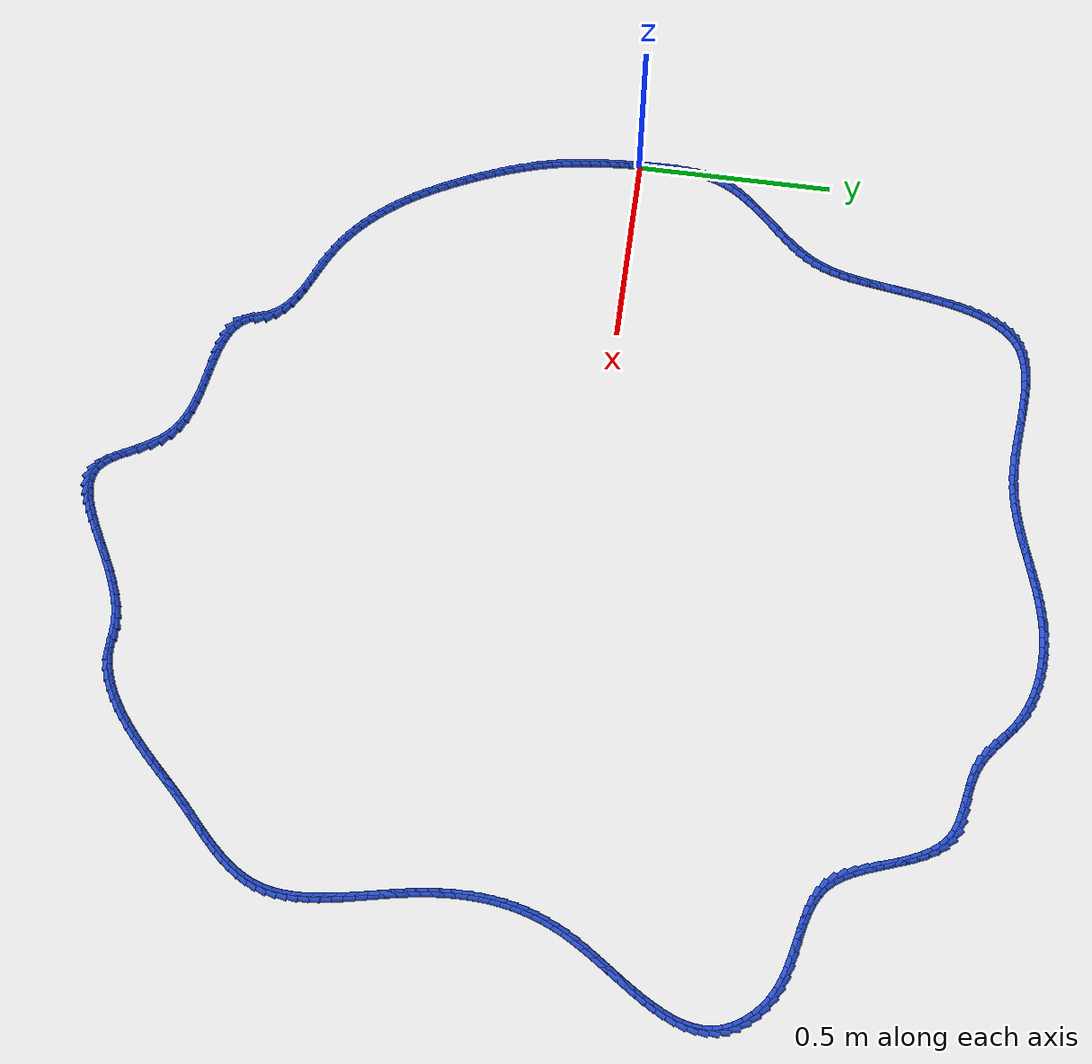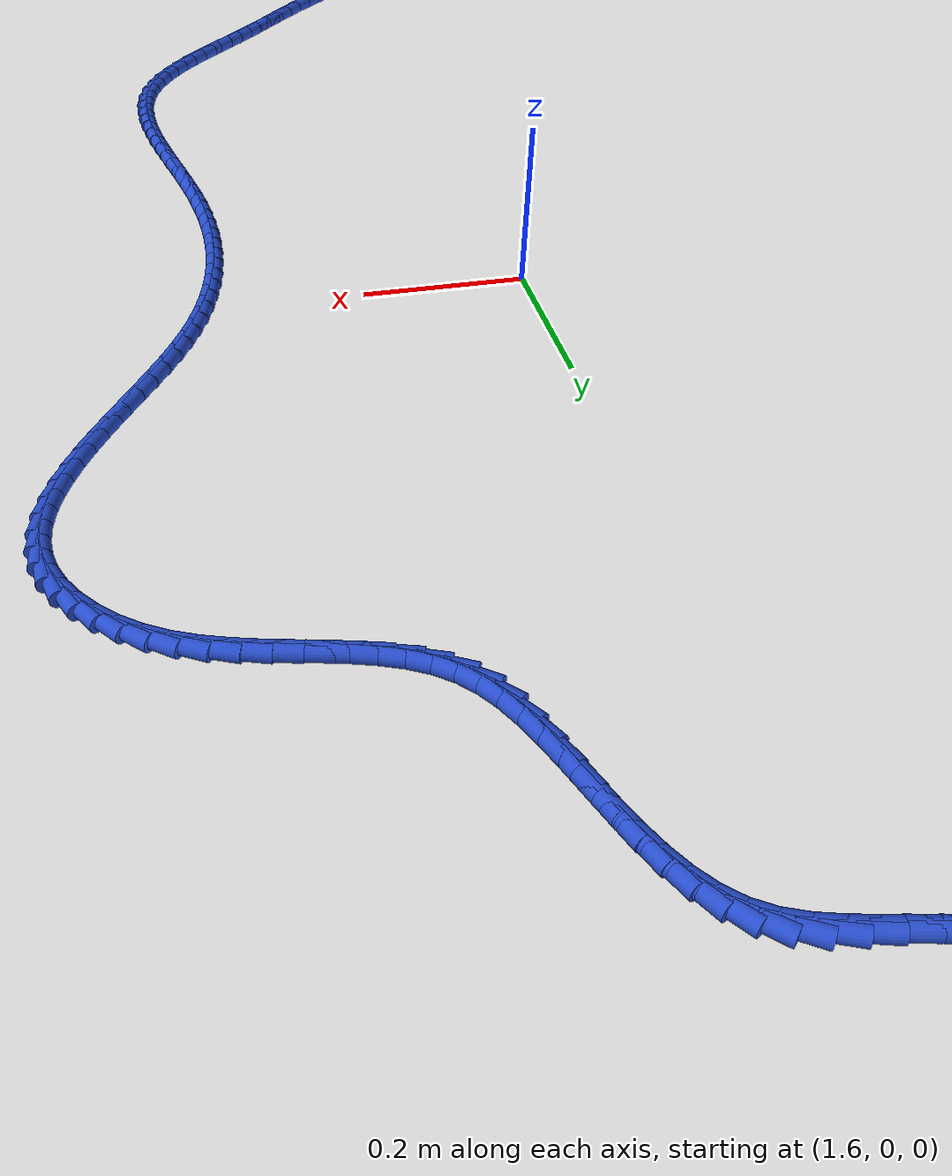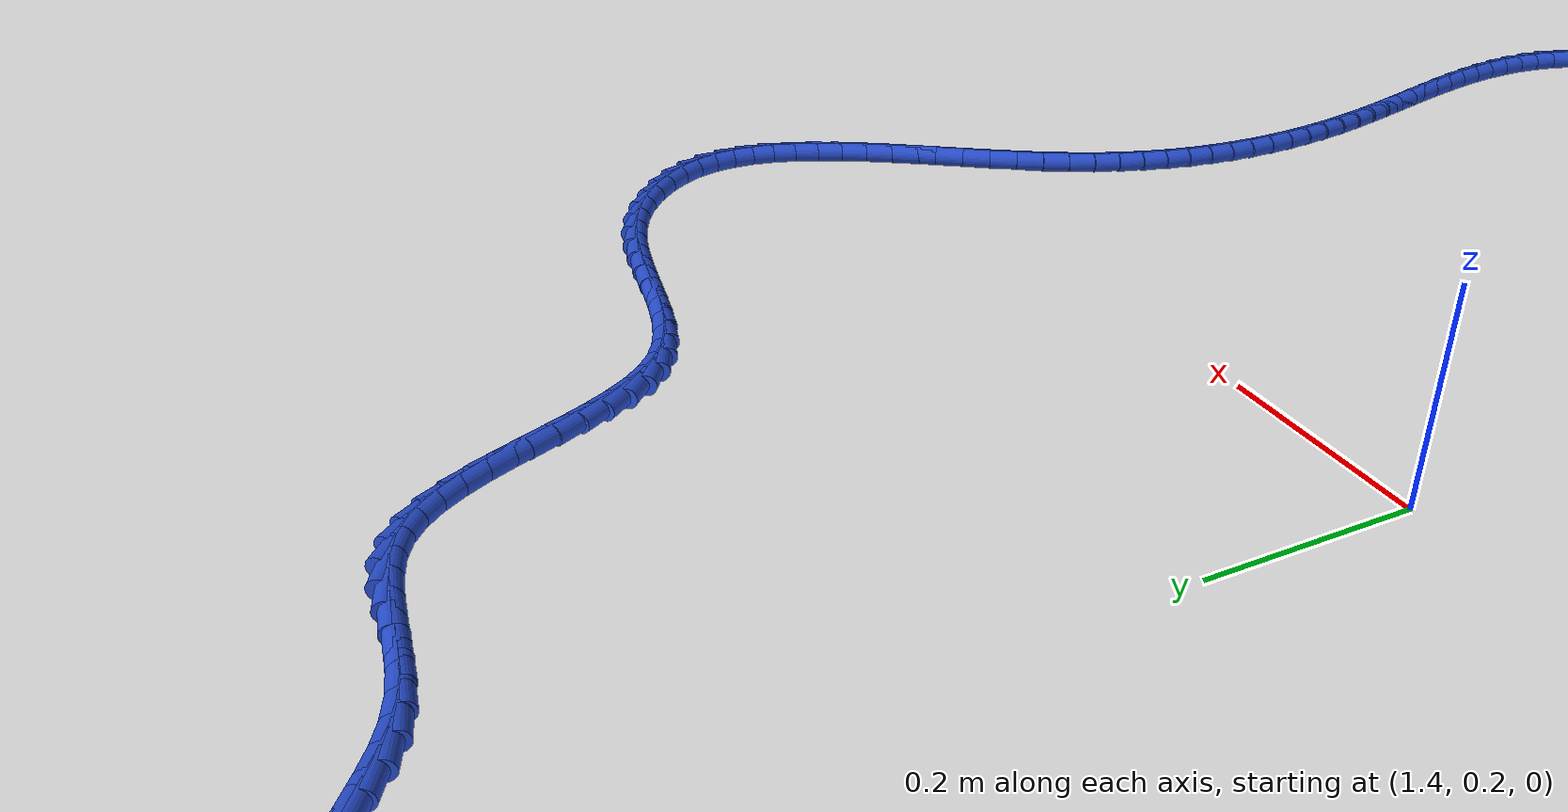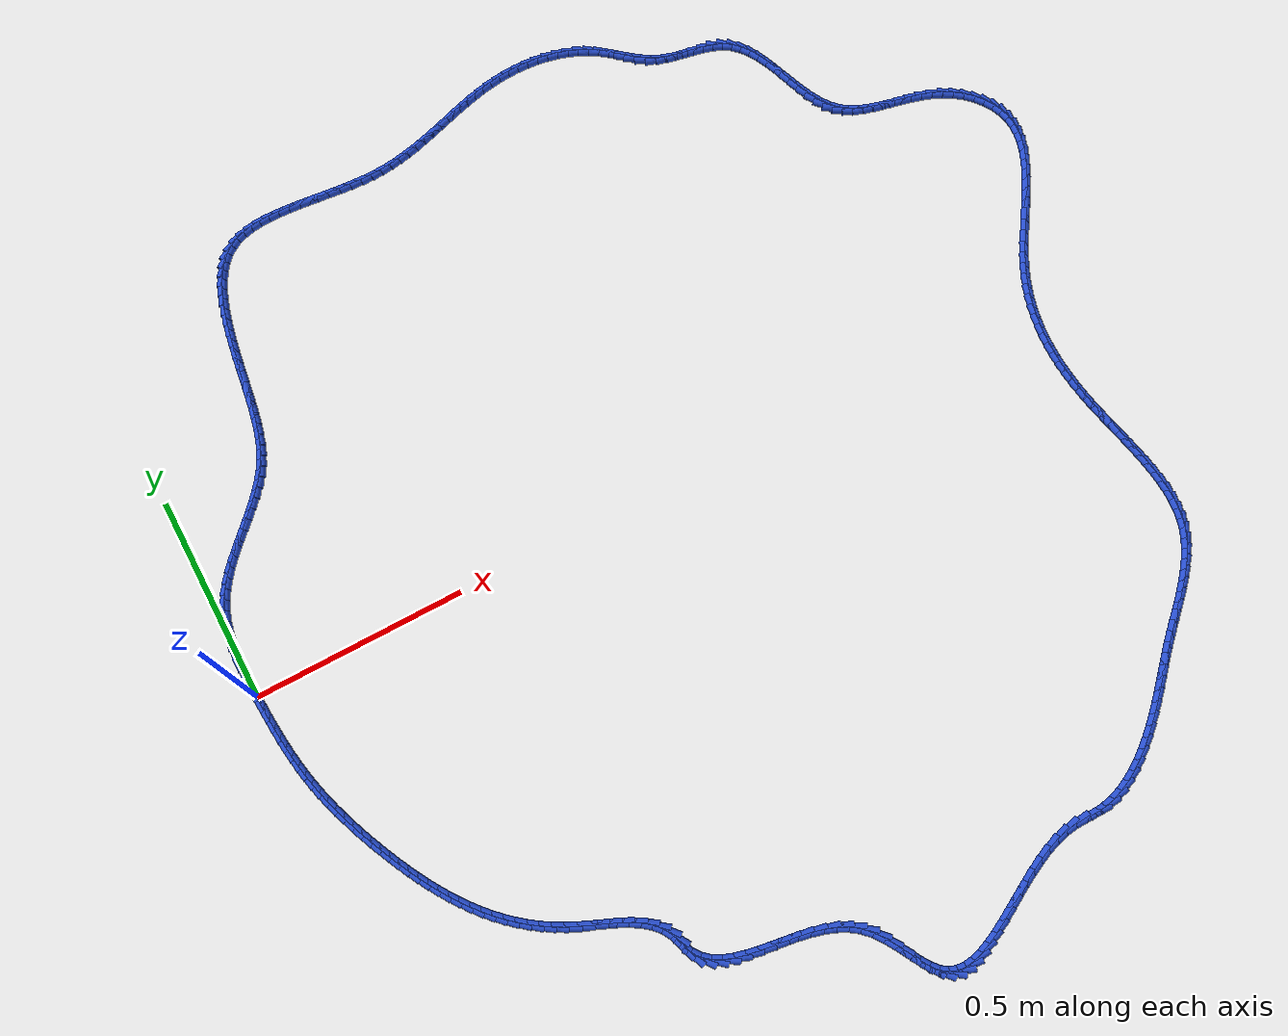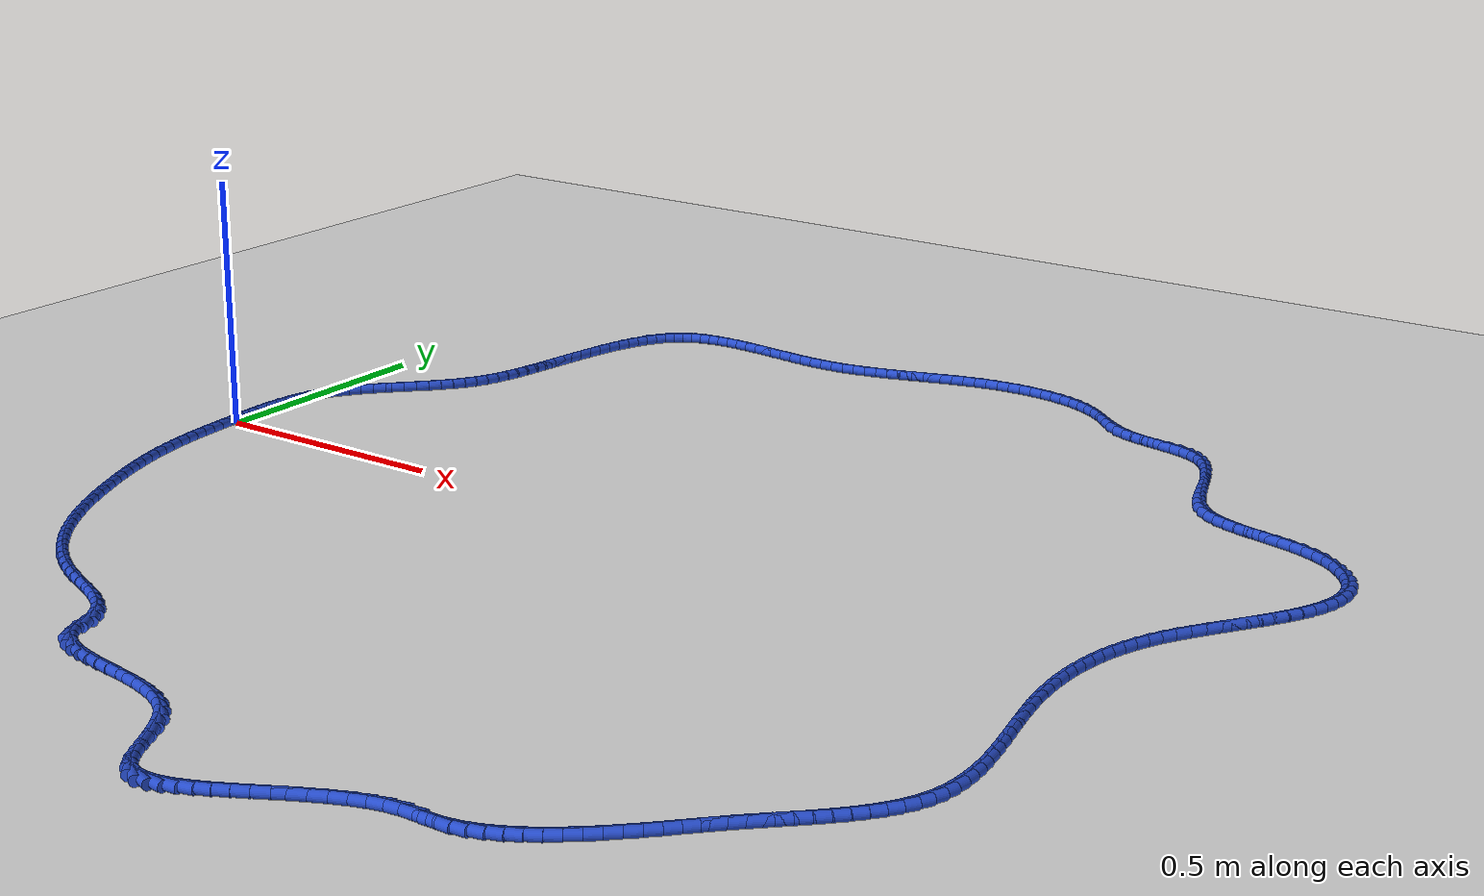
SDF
<sdf version="1.6">
 <world name="default">
  <light name="sun" type="directional">
   <pose>0 0 10 0 -0 0</pose>
   <diffuse>0.8 0.8 0.8 1</diffuse>
   <specular>0.2 0.2 0.2 1</specular>
   <attenuation>
    <range>1000</range>
    <constant>0.9</constant>
    <linear>0.01</linear>
    <quadratic>0.001</quadratic>
   </attenuation>
   <direction>-0.5 0.1 -0.9</direction>
  </light>
  <model name="ground_plane">
   <static>1</static>
   <link name="link">
    <collision name="collision">
     <geometry><plane><normal>0 0 1</normal><size>100 100</size></plane></geometry>
     <surface><friction><ode><mu>100</mu><mu2>50</mu2></ode></friction></surface>
    </collision>
    <visual name="visual">
     <cast_shadows>0</cast_shadows>
     <geometry><plane><normal>0 0 1</normal><size>100 100</size></plane></geometry>
     <material>
      <script><uri>file://media/materials/scripts/gazebo.material</uri><name>Gazebo/WhiteGlow</name></script>
     </material>
    </visual>
   </link>
  </model>
  <gravity>0 0 -9.8</gravity>
  <magnetic_field>6e-06 2.3e-05 -4.2e-05</magnetic_field>
  <atmosphere type="adiabatic"/>
  <physics name="default_physics" default="0" type="ode">
   <max_step_size>0.001</max_step_size>
   <real_time_factor>1</real_time_factor>
   <real_time_update_rate>1000</real_time_update_rate>
  </physics>
  <scene><ambient>0.4 0.4 0.4 1</ambient><background>0.7 0.7 0.7 1</background><shadows>1</shadows></scene>
  <spherical_coordinates>
   <surface_model>EARTH_WGS84</surface_model>
   <latitude_deg>0</latitude_deg>
   <longitude_deg>0</longitude_deg>
   <elevation>0</elevation>
   <heading_deg>0</heading_deg>
  </spherical_coordinates>
  <model name="line">
   <link name="link_0">
    <pose>-7.806255641895632e-18 -2.7755575615628914e-17 0.01 0 1.57 -1.5313961069417978</pose>
    <collision name="collision">
     <geometry><cylinder><radius>0.01</radius><length>0.08</length></cylinder></geometry>
    </collision>
    <visual name="visual">
     <material>
      <script><name>Gazebo/Blue</name><uri>file://media/materials/scripts/gazebo.material</uri></script>
     </material>
     <geometry><cylinder><radius>0.01</radius><length>0.08</length></cylinder></geometry>
    </visual>
   </link>
   <link name="link_1">
    <pose>-0.0010407498841887648 0.026401154278248604 0.01 0 1.57 -1.5477498399603729</pose>
    <collision name="collision">
     <geometry><cylinder><radius>0.01</radius><length>0.08</length></cylinder></geometry>
    </collision>
    <visual name="visual">
     <material>
      <script><name>Gazebo/Blue</name><uri>file://media/materials/scripts/gazebo.material</uri></script>
     </material>
     <geometry><cylinder><radius>0.01</radius><length>0.08</length></cylinder></geometry>
    </visual>
   </link>
   <link name="link_2">
    <pose>-0.001651303130338141 0.05288871180380666 0.01 0 1.57 1.5679038501124116</pose>
    <collision name="collision">
     <geometry><cylinder><radius>0.01</radius><length>0.08</length></cylinder></geometry>
    </collision>
    <visual name="visual">
     <material>
      <script><name>Gazebo/Blue</name><uri>file://media/materials/scripts/gazebo.material</uri></script>
     </material>
     <geometry><cylinder><radius>0.01</radius><length>0.08</length></cylinder></geometry>
    </visual>
   </link>
   <link name="link_3">
    <pose>-0.0015748714768153258 0.07931293186144053 0.01 0 1.57 1.5318934016315766</pose>
    <collision name="collision">
     <geometry><cylinder><radius>0.01</radius><length>0.08</length></cylinder></geometry>
    </collision>
    <visual name="visual">
     <material>
      <script><name>Gazebo/Blue</name><uri>file://media/materials/scripts/gazebo.material</uri></script>
     </material>
     <geometry><cylinder><radius>0.01</radius><length>0.08</length></cylinder></geometry>
    </visual>
   </link>
   <link name="link_4">
    <pose>-0.0005546666619875092 0.10552407373591659 0.01 0 1.57 1.4850914954284056</pose>
    <collision name="collision">
     <geometry><cylinder><radius>0.01</radius><length>0.08</length></cylinder></geometry>
    </collision>
    <visual name="visual">
     <material>
      <script><name>Gazebo/Blue</name><uri>file://media/materials/scripts/gazebo.material</uri></script>
     </material>
     <geometry><cylinder><radius>0.01</radius><length>0.08</length></cylinder></geometry>
    </visual>
   </link>
   <link name="link_5">
    <pose>0.0016660995757781182 0.13137239671200127 0.01 0 1.57 1.4266286491698912</pose>
    <collision name="collision">
     <geometry><cylinder><radius>0.01</radius><length>0.08</length></cylinder></geometry>
    </collision>
    <visual name="visual">
     <material>
      <script><name>Gazebo/Blue</name><uri>file://media/materials/scripts/gazebo.material</uri></script>
     </material>
     <geometry><cylinder><radius>0.01</radius><length>0.08</length></cylinder></geometry>
    </visual>
   </link>
   <link name="link_6">
    <pose>0.005344215498114369 0.15670816007446092 0.01 0 1.57 1.3556345875797808</pose>
    <collision name="collision">
     <geometry><cylinder><radius>0.01</radius><length>0.08</length></cylinder></geometry>
    </collision>
    <visual name="visual">
     <material>
      <script><name>Gazebo/Blue</name><uri>file://media/materials/scripts/gazebo.material</uri></script>
     </material>
     <geometry><cylinder><radius>0.01</radius><length>0.08</length></cylinder></geometry>
    </visual>
   </link>
   <link name="link_7">
    <pose>0.010736469366654046 0.18138162310806194 0.01 0 1.57 1.271485818599171</pose>
    <collision name="collision">
     <geometry><cylinder><radius>0.01</radius><length>0.08</length></cylinder></geometry>
    </collision>
    <visual name="visual">
     <material>
      <script><name>Gazebo/Blue</name><uri>file://media/materials/scripts/gazebo.material</uri></script>
     </material>
     <geometry><cylinder><radius>0.01</radius><length>0.08</length></cylinder></geometry>
    </visual>
   </link>
   <link name="link_8">
    <pose>0.01809964944302997 0.20524304509757088 0.01 0 1.57 1.1742409841898394</pose>
    <collision name="collision">
     <geometry><cylinder><radius>0.01</radius><length>0.08</length></cylinder></geometry>
    </collision>
    <visual name="visual">
     <material>
      <script><name>Gazebo/Blue</name><uri>file://media/materials/scripts/gazebo.material</uri></script>
     </material>
     <geometry><cylinder><radius>0.01</radius><length>0.08</length></cylinder></geometry>
    </visual>
   </link>
   <link name="link_9">
    <pose>0.027688948665799223 0.22814348191232364 0.01 0 1.57 1.0736087766955555</pose>
    <collision name="collision">
     <geometry><cylinder><radius>0.01</radius><length>0.08</length></cylinder></geometry>
    </collision>
    <visual name="visual">
     <material>
      <script><name>Gazebo/Blue</name><uri>file://media/materials/scripts/gazebo.material</uri></script>
     </material>
     <geometry><cylinder><radius>0.01</radius><length>0.08</length></cylinder></geometry>
    </visual>
   </link>
   <link name="link_10">
    <pose>0.03956611918923954 0.250030579226104 0.01 0 1.57 0.9879249587448946</pose>
    <collision name="collision">
     <geometry><cylinder><radius>0.01</radius><length>0.08</length></cylinder></geometry>
    </collision>
    <visual name="visual">
     <material>
      <script><name>Gazebo/Blue</name><uri>file://media/materials/scripts/gazebo.material</uri></script>
     </material>
     <geometry><cylinder><radius>0.01</radius><length>0.08</length></cylinder></geometry>
    </visual>
   </link>
   <link name="link_11">
    <pose>0.05341700344949822 0.2710396838032357 0.01 0 1.57 0.919418216857093</pose>
    <collision name="collision">
     <geometry><cylinder><radius>0.01</radius><length>0.08</length></cylinder></geometry>
    </collision>
    <visual name="visual">
     <material>
      <script><name>Gazebo/Blue</name><uri>file://media/materials/scripts/gazebo.material</uri></script>
     </material>
     <geometry><cylinder><radius>0.01</radius><length>0.08</length></cylinder></geometry>
    </visual>
   </link>
   <link name="link_12">
    <pose>0.06888422368421243 0.29132772333027546 0.01 0 1.57 0.8674553870164292</pose>
    <collision name="collision">
     <geometry><cylinder><radius>0.01</radius><length>0.08</length></cylinder></geometry>
    </collision>
    <visual name="visual">
     <material>
      <script><name>Gazebo/Blue</name><uri>file://media/materials/scripts/gazebo.material</uri></script>
     </material>
     <geometry><cylinder><radius>0.01</radius><length>0.08</length></cylinder></geometry>
    </visual>
   </link>
   <link name="link_13">
    <pose>0.08561040213101945 0.3110516254937802 0.01 0 1.57 0.8310818433353483</pose>
    <collision name="collision">
     <geometry><cylinder><radius>0.01</radius><length>0.08</length></cylinder></geometry>
    </collision>
    <visual name="visual">
     <material>
      <script><name>Gazebo/Blue</name><uri>file://media/materials/scripts/gazebo.material</uri></script>
     </material>
     <geometry><cylinder><radius>0.01</radius><length>0.08</length></cylinder></geometry>
    </visual>
   </link>
   <link name="link_14">
    <pose>0.10323816102755638 0.3303683179803069 0.01 0 1.57 0.8094130949772309</pose>
    <collision name="collision">
     <geometry><cylinder><radius>0.01</radius><length>0.08</length></cylinder></geometry>
    </collision>
    <visual name="visual">
     <material>
      <script><name>Gazebo/Blue</name><uri>file://media/materials/scripts/gazebo.material</uri></script>
     </material>
     <geometry><cylinder><radius>0.01</radius><length>0.08</length></cylinder></geometry>
    </visual>
   </link>
   <link name="link_15">
    <pose>0.12141012261146059 0.3494347284764126 0.01 0 1.57 0.8018509878825213</pose>
    <collision name="collision">
     <geometry><cylinder><radius>0.01</radius><length>0.08</length></cylinder></geometry>
    </collision>
    <visual name="visual">
     <material>
      <script><name>Gazebo/Blue</name><uri>file://media/materials/scripts/gazebo.material</uri></script>
     </material>
     <geometry><cylinder><radius>0.01</radius><length>0.08</length></cylinder></geometry>
    </visual>
   </link>
   <link name="link_16">
    <pose>0.13976890912036913 0.36840778466865387 0.01 0 1.57 0.8081853271306338</pose>
    <collision name="collision">
     <geometry><cylinder><radius>0.01</radius><length>0.08</length></cylinder></geometry>
    </collision>
    <visual name="visual">
     <material>
      <script><name>Gazebo/Blue</name><uri>file://media/materials/scripts/gazebo.material</uri></script>
     </material>
     <geometry><cylinder><radius>0.01</radius><length>0.08</length></cylinder></geometry>
    </visual>
   </link>
   <link name="link_17">
    <pose>0.15795714279191925 0.3874444142435878 0.01 0 1.57 0.8286252430602973</pose>
    <collision name="collision">
     <geometry><cylinder><radius>0.01</radius><length>0.08</length></cylinder></geometry>
    </collision>
    <visual name="visual">
     <material>
      <script><name>Gazebo/Blue</name><uri>file://media/materials/scripts/gazebo.material</uri></script>
     </material>
     <geometry><cylinder><radius>0.01</radius><length>0.08</length></cylinder></geometry>
    </visual>
   </link>
   <link name="link_18">
    <pose>0.17561744586374822 0.40670154488777144 0.01 0 1.57 0.863776128324235</pose>
    <collision name="collision">
     <geometry><cylinder><radius>0.01</radius><length>0.08</length></cylinder></geometry>
    </collision>
    <visual name="visual">
     <material>
      <script><name>Gazebo/Blue</name><uri>file://media/materials/scripts/gazebo.material</uri></script>
     </material>
     <geometry><cylinder><radius>0.01</radius><length>0.08</length></cylinder></geometry>
    </visual>
   </link>
   <link name="link_19">
    <pose>0.19239244057349317 0.42633610428776136 0.01 0 1.57 0.9145477840002221</pose>
    <collision name="collision">
     <geometry><cylinder><radius>0.01</radius><length>0.08</length></cylinder></geometry>
    </collision>
    <visual name="visual">
     <material>
      <script><name>Gazebo/Blue</name><uri>file://media/materials/scripts/gazebo.material</uri></script>
     </material>
     <geometry><cylinder><radius>0.01</radius><length>0.08</length></cylinder></geometry>
    </visual>
   </link>
   <link name="link_20">
    <pose>0.20792474915879142 0.4465050201301148 0.01 0 1.57 0.9819497400595649</pose>
    <collision name="collision">
     <geometry><cylinder><radius>0.01</radius><length>0.08</length></cylinder></geometry>
    </collision>
    <visual name="visual">
     <material>
      <script><name>Gazebo/Blue</name><uri>file://media/materials/scripts/gazebo.material</uri></script>
     </material>
     <geometry><cylinder><radius>0.01</radius><length>0.08</length></cylinder></geometry>
    </visual>
   </link>
   <link name="link_21">
    <pose>0.22185699385728008 0.4673652201013885 0.01 0 1.57 1.0664495328248198</pose>
    <collision name="collision">
     <geometry><cylinder><radius>0.01</radius><length>0.08</length></cylinder></geometry>
    </collision>
    <visual name="visual">
     <material>
      <script><name>Gazebo/Blue</name><uri>file://media/materials/scripts/gazebo.material</uri></script>
     </material>
     <geometry><cylinder><radius>0.01</radius><length>0.08</length></cylinder></geometry>
    </visual>
   </link>
   <link name="link_22">
    <pose>0.23383828106783672 0.48907202196712984 0.01 0 1.57 1.1566327027704366</pose>
    <collision name="collision">
     <geometry><cylinder><radius>0.01</radius><length>0.08</length></cylinder></geometry>
    </collision>
    <visual name="visual">
     <material>
      <script><name>Gazebo/Blue</name><uri>file://media/materials/scripts/gazebo.material</uri></script>
     </material>
     <geometry><cylinder><radius>0.01</radius><length>0.08</length></cylinder></geometry>
    </visual>
   </link>
   <link name="link_23">
    <pose>0.24379099006312477 0.5117128938937678 0.01 0 1.57 1.2354678965027972</pose>
    <collision name="collision">
     <geometry><cylinder><radius>0.01</radius><length>0.08</length></cylinder></geometry>
    </collision>
    <visual name="visual">
     <material>
      <script><name>Gazebo/Blue</name><uri>file://media/materials/scripts/gazebo.material</uri></script>
     </material>
     <geometry><cylinder><radius>0.01</radius><length>0.08</length></cylinder></geometry>
    </visual>
   </link>
   <link name="link_24">
    <pose>0.2520052679101452 0.5352839927621693 0.01 0 1.57 1.3002728856279933</pose>
    <collision name="collision">
     <geometry><cylinder><radius>0.01</radius><length>0.08</length></cylinder></geometry>
    </collision>
    <visual name="visual">
     <material>
      <script><name>Gazebo/Blue</name><uri>file://media/materials/scripts/gazebo.material</uri></script>
     </material>
     <geometry><cylinder><radius>0.01</radius><length>0.08</length></cylinder></geometry>
    </visual>
   </link>
   <link name="link_25">
    <pose>0.25879716888585014 0.5597750430774397 0.01 0 1.57 1.3505907689030405</pose>
    <collision name="collision">
     <geometry><cylinder><radius>0.01</radius><length>0.08</length></cylinder></geometry>
    </collision>
    <visual name="visual">
     <material>
      <script><name>Gazebo/Blue</name><uri>file://media/materials/scripts/gazebo.material</uri></script>
     </material>
     <geometry><cylinder><radius>0.01</radius><length>0.08</length></cylinder></geometry>
    </visual>
   </link>
   <link name="link_26">
    <pose>0.2644827472671916 0.5851757693446847 0.01 0 1.57 1.386769696493441</pose>
    <collision name="collision">
     <geometry><cylinder><radius>0.01</radius><length>0.08</length></cylinder></geometry>
    </collision>
    <visual name="visual">
     <material>
      <script><name>Gazebo/Blue</name><uri>file://media/materials/scripts/gazebo.material</uri></script>
     </material>
     <geometry><cylinder><radius>0.01</radius><length>0.08</length></cylinder></geometry>
    </visual>
   </link>
   <link name="link_27">
    <pose>0.2693780573311219 0.6114758960690103 0.01 0 1.57 1.409644637521641</pose>
    <collision name="collision">
     <geometry><cylinder><radius>0.01</radius><length>0.08</length></cylinder></geometry>
    </collision>
    <visual name="visual">
     <material>
      <script><name>Gazebo/Blue</name><uri>file://media/materials/scripts/gazebo.material</uri></script>
     </material>
     <geometry><cylinder><radius>0.01</radius><length>0.08</length></cylinder></geometry>
    </visual>
   </link>
   <link name="link_28">
    <pose>0.27379764245828614 0.6386630764530923 0.01 0 1.57 1.4220846654886226</pose>
    <collision name="collision">
     <geometry><cylinder><radius>0.01</radius><length>0.08</length></cylinder></geometry>
    </collision>
    <visual name="visual">
     <material>
      <script><name>Gazebo/Blue</name><uri>file://media/materials/scripts/gazebo.material</uri></script>
     </material>
     <geometry><cylinder><radius>0.01</radius><length>0.08</length></cylinder></geometry>
    </visual>
   </link>
   <link name="link_29">
    <pose>0.27798779150113667 0.6666313929036211 0.01 0 1.57 1.427559347863563</pose>
    <collision name="collision">
     <geometry><cylinder><radius>0.01</radius><length>0.08</length></cylinder></geometry>
    </collision>
    <visual name="visual">
     <material>
      <script><name>Gazebo/Blue</name><uri>file://media/materials/scripts/gazebo.material</uri></script>
     </material>
     <geometry><cylinder><radius>0.01</radius><length>0.08</length></cylinder></geometry>
    </visual>
   </link>
   <link name="link_30">
    <pose>0.2821001914309753 0.6951452371890935 0.01 0 1.57 1.4267551082049765</pose>
    <collision name="collision">
     <geometry><cylinder><radius>0.01</radius><length>0.08</length></cylinder></geometry>
    </collision>
    <visual name="visual">
     <material>
      <script><name>Gazebo/Blue</name><uri>file://media/materials/scripts/gazebo.material</uri></script>
     </material>
     <geometry><cylinder><radius>0.01</radius><length>0.08</length></cylinder></geometry>
    </visual>
   </link>
   <link name="link_31">
    <pose>0.2862795722002132 0.7239594636332021 0.01 0 1.57 1.419851659040207</pose>
    <collision name="collision">
     <geometry><cylinder><radius>0.01</radius><length>0.08</length></cylinder></geometry>
    </collision>
    <visual name="visual">
     <material>
      <script><name>Gazebo/Blue</name><uri>file://media/materials/scripts/gazebo.material</uri></script>
     </material>
     <geometry><cylinder><radius>0.01</radius><length>0.08</length></cylinder></geometry>
    </visual>
   </link>
   <link name="link_32">
    <pose>0.29067066376126144 0.7528289265596388 0.01 0 1.57 1.406746815121965</pose>
    <collision name="collision">
     <geometry><cylinder><radius>0.01</radius><length>0.08</length></cylinder></geometry>
    </collision>
    <visual name="visual">
     <material>
      <script><name>Gazebo/Blue</name><uri>file://media/materials/scripts/gazebo.material</uri></script>
     </material>
     <geometry><cylinder><radius>0.01</radius><length>0.08</length></cylinder></geometry>
    </visual>
   </link>
   <link name="link_33">
    <pose>0.2954181960665311 0.7815084802920962 0.01 0 1.57 1.3870611959013026</pose>
    <collision name="collision">
     <geometry><cylinder><radius>0.01</radius><length>0.08</length></cylinder></geometry>
    </collision>
    <visual name="visual">
     <material>
      <script><name>Gazebo/Blue</name><uri>file://media/materials/scripts/gazebo.material</uri></script>
     </material>
     <geometry><cylinder><radius>0.01</radius><length>0.08</length></cylinder></geometry>
    </visual>
   </link>
   <link name="link_34">
    <pose>0.3006668990684332 0.8097529791542658 0.01 0 1.57 1.360120363509948</pose>
    <collision name="collision">
     <geometry><cylinder><radius>0.01</radius><length>0.08</length></cylinder></geometry>
    </collision>
    <visual name="visual">
     <material>
      <script><name>Gazebo/Blue</name><uri>file://media/materials/scripts/gazebo.material</uri></script>
     </material>
     <geometry><cylinder><radius>0.01</radius><length>0.08</length></cylinder></geometry>
    </visual>
   </link>
   <link name="link_35">
    <pose>0.3065615027193788 0.8373172774698407 0.01 0 1.57 1.3249170636117835</pose>
    <collision name="collision">
     <geometry><cylinder><radius>0.01</radius><length>0.08</length></cylinder></geometry>
    </collision>
    <visual name="visual">
     <material>
      <script><name>Gazebo/Blue</name><uri>file://media/materials/scripts/gazebo.material</uri></script>
     </material>
     <geometry><cylinder><radius>0.01</radius><length>0.08</length></cylinder></geometry>
    </visual>
   </link>
   <link name="link_36">
    <pose>0.31324673697177907 0.8639562295625131 0.01 0 1.57 1.2800580878205712</pose>
    <collision name="collision">
     <geometry><cylinder><radius>0.01</radius><length>0.08</length></cylinder></geometry>
    </collision>
    <visual name="visual">
     <material>
      <script><name>Gazebo/Blue</name><uri>file://media/materials/scripts/gazebo.material</uri></script>
     </material>
     <geometry><cylinder><radius>0.01</radius><length>0.08</length></cylinder></geometry>
    </visual>
   </link>
   <link name="link_37">
    <pose>0.32086733177804494 0.8894246897559747 0.01 0 1.57 1.2237079512460936</pose>
    <collision name="collision">
     <geometry><cylinder><radius>0.01</radius><length>0.08</length></cylinder></geometry>
    </collision>
    <visual name="visual">
     <material>
      <script><name>Gazebo/Blue</name><uri>file://media/materials/scripts/gazebo.material</uri></script>
     </material>
     <geometry><cylinder><radius>0.01</radius><length>0.08</length></cylinder></geometry>
    </visual>
   </link>
   <link name="link_38">
    <pose>0.3295680170905876 0.9134775123739178 0.01 0 1.57 1.1535611157842798</pose>
    <collision name="collision">
     <geometry><cylinder><radius>0.01</radius><length>0.08</length></cylinder></geometry>
    </collision>
    <visual name="visual">
     <material>
      <script><name>Gazebo/Blue</name><uri>file://media/materials/scripts/gazebo.material</uri></script>
     </material>
     <geometry><cylinder><radius>0.01</radius><length>0.08</length></cylinder></geometry>
    </visual>
   </link>
   <link name="link_39">
    <pose>0.3394935228618183 0.9358695517400353 0.01 0 1.57 1.0669157712887294</pose>
    <collision name="collision">
     <geometry><cylinder><radius>0.01</radius><length>0.08</length></cylinder></geometry>
    </collision>
    <visual name="visual">
     <material>
      <script><name>Gazebo/Blue</name><uri>file://media/materials/scripts/gazebo.material</uri></script>
     </material>
     <geometry><cylinder><radius>0.01</radius><length>0.08</length></cylinder></geometry>
    </visual>
   </link>
   <link name="link_40">
    <pose>0.3507885790441476 0.9563556621780187 0.01 0 1.57 0.96099296609431</pose>
    <collision name="collision">
     <geometry><cylinder><radius>0.01</radius><length>0.08</length></cylinder></geometry>
    </collision>
    <visual name="visual">
     <material>
      <script><name>Gazebo/Blue</name><uri>file://media/materials/scripts/gazebo.material</uri></script>
     </material>
     <geometry><cylinder><radius>0.01</radius><length>0.08</length></cylinder></geometry>
    </visual>
   </link>
   <link name="link_41">
    <pose>0.3635979155899872 0.974690698011561 0.01 0 1.57 0.8337198050977895</pose>
    <collision name="collision">
     <geometry><cylinder><radius>0.01</radius><length>0.08</length></cylinder></geometry>
    </collision>
    <visual name="visual">
     <material>
      <script><name>Gazebo/Blue</name><uri>file://media/materials/scripts/gazebo.material</uri></script>
     </material>
     <geometry><cylinder><radius>0.01</radius><length>0.08</length></cylinder></geometry>
    </visual>
   </link>
   <link name="link_42">
    <pose>0.37806626245174757 0.9906295135643537 0.01 0 1.57 0.6851374240069088</pose>
    <collision name="collision">
     <geometry><cylinder><radius>0.01</radius><length>0.08</length></cylinder></geometry>
    </collision>
    <visual name="visual">
     <material>
      <script><name>Gazebo/Blue</name><uri>file://media/materials/scripts/gazebo.material</uri></script>
     </material>
     <geometry><cylinder><radius>0.01</radius><length>0.08</length></cylinder></geometry>
    </visual>
   </link>
   <link name="link_43">
    <pose>0.3943383495818402 1.0039269631600896 0.01 0 1.57 0.5220859281121061</pose>
    <collision name="collision">
     <geometry><cylinder><radius>0.01</radius><length>0.08</length></cylinder></geometry>
    </collision>
    <visual name="visual">
     <material>
      <script><name>Gazebo/Blue</name><uri>file://media/materials/scripts/gazebo.material</uri></script>
     </material>
     <geometry><cylinder><radius>0.01</radius><length>0.08</length></cylinder></geometry>
    </visual>
   </link>
   <link name="link_44">
    <pose>0.4125269788089199 1.0143915163008872 0.01 0 1.57 0.3712828970342463</pose>
    <collision name="collision">
     <geometry><cylinder><radius>0.01</radius><length>0.08</length></cylinder></geometry>
    </collision>
    <visual name="visual">
     <material>
      <script><name>Gazebo/Blue</name><uri>file://media/materials/scripts/gazebo.material</uri></script>
     </material>
     <geometry><cylinder><radius>0.01</radius><length>0.08</length></cylinder></geometry>
    </visual>
   </link>
   <link name="link_45">
    <pose>0.43253633831968685 1.0221819561408974 0.01 0 1.57 0.2451162470799167</pose>
    <collision name="collision">
     <geometry><cylinder><radius>0.01</radius><length>0.08</length></cylinder></geometry>
    </collision>
    <visual name="visual">
     <material>
      <script><name>Gazebo/Blue</name><uri>file://media/materials/scripts/gazebo.material</uri></script>
     </material>
     <geometry><cylinder><radius>0.01</radius><length>0.08</length></cylinder></geometry>
    </visual>
   </link>
   <link name="link_46">
    <pose>0.4541868401345629 1.027597746637728 0.01 0 1.57 0.14356287580195579</pose>
    <collision name="collision">
     <geometry><cylinder><radius>0.01</radius><length>0.08</length></cylinder></geometry>
    </collision>
    <visual name="visual">
     <material>
      <script><name>Gazebo/Blue</name><uri>file://media/materials/scripts/gazebo.material</uri></script>
     </material>
     <geometry><cylinder><radius>0.01</radius><length>0.08</length></cylinder></geometry>
    </visual>
   </link>
   <link name="link_47">
    <pose>0.4772986699005165 1.030938731885734 0.01 0 1.57 0.06411084877383419</pose>
    <collision name="collision">
     <geometry><cylinder><radius>0.01</radius><length>0.08</length></cylinder></geometry>
    </collision>
    <visual name="visual">
     <material>
      <script><name>Gazebo/Blue</name><uri>file://media/materials/scripts/gazebo.material</uri></script>
     </material>
     <geometry><cylinder><radius>0.01</radius><length>0.08</length></cylinder></geometry>
    </visual>
   </link>
   <link name="link_48">
    <pose>0.5016920132645161 1.0325047559792688 0.01 0 1.57 0.0035656597853853346</pose>
    <collision name="collision">
     <geometry><cylinder><radius>0.01</radius><length>0.08</length></cylinder></geometry>
    </collision>
    <visual name="visual">
     <material>
      <script><name>Gazebo/Blue</name><uri>file://media/materials/scripts/gazebo.material</uri></script>
     </material>
     <geometry><cylinder><radius>0.01</radius><length>0.08</length></cylinder></geometry>
    </visual>
   </link>
   <link name="link_49">
    <pose>0.5271870558735302 1.0325956630126887 0.01 0 1.57 -0.041025115922587826</pose>
    <collision name="collision">
     <geometry><cylinder><radius>0.01</radius><length>0.08</length></cylinder></geometry>
    </collision>
    <visual name="visual">
     <material>
      <script><name>Gazebo/Blue</name><uri>file://media/materials/scripts/gazebo.material</uri></script>
     </material>
     <geometry><cylinder><radius>0.01</radius><length>0.08</length></cylinder></geometry>
    </visual>
   </link>
   <link name="link_50">
    <pose>0.5536039833745275 1.0315112970803466 0.01 0 1.57 -0.07203519770259051</pose>
    <collision name="collision">
     <geometry><cylinder><radius>0.01</radius><length>0.08</length></cylinder></geometry>
    </collision>
    <visual name="visual">
     <material>
      <script><name>Gazebo/Blue</name><uri>file://media/materials/scripts/gazebo.material</uri></script>
     </material>
     <geometry><cylinder><radius>0.01</radius><length>0.08</length></cylinder></geometry>
    </visual>
   </link>
   <link name="link_51">
    <pose>0.5807629814144761 1.029551502276598 0.01 0 1.57 -0.09120602697447878</pose>
    <collision name="collision">
     <geometry><cylinder><radius>0.01</radius><length>0.08</length></cylinder></geometry>
    </collision>
    <visual name="visual">
     <material>
      <script><name>Gazebo/Blue</name><uri>file://media/materials/scripts/gazebo.material</uri></script>
     </material>
     <geometry><cylinder><radius>0.01</radius><length>0.08</length></cylinder></geometry>
    </visual>
   </link>
   <link name="link_52">
    <pose>0.6084842356403452 1.027016122695797 0.01 0 1.57 -0.09969509824413124</pose>
    <collision name="collision">
     <geometry><cylinder><radius>0.01</radius><length>0.08</length></cylinder></geometry>
    </collision>
    <visual name="visual">
     <material>
      <script><name>Gazebo/Blue</name><uri>file://media/materials/scripts/gazebo.material</uri></script>
     </material>
     <geometry><cylinder><radius>0.01</radius><length>0.08</length></cylinder></geometry>
    </visual>
   </link>
   <link name="link_53">
    <pose>0.6365879316991025 1.0242050024322984 0.01 0 1.57 -0.09814283721443187</pose>
    <collision name="collision">
     <geometry><cylinder><radius>0.01</radius><length>0.08</length></cylinder></geometry>
    </collision>
    <visual name="visual">
     <material>
      <script><name>Gazebo/Blue</name><uri>file://media/materials/scripts/gazebo.material</uri></script>
     </material>
     <geometry><cylinder><radius>0.01</radius><length>0.08</length></cylinder></geometry>
    </visual>
   </link>
   <link name="link_54">
    <pose>0.6648942552377173 1.0214179855804564 0.01 0 1.57 -0.08672664268167486</pose>
    <collision name="collision">
     <geometry><cylinder><radius>0.01</radius><length>0.08</length></cylinder></geometry>
    </collision>
    <visual name="visual">
     <material>
      <script><name>Gazebo/Blue</name><uri>file://media/materials/scripts/gazebo.material</uri></script>
     </material>
     <geometry><cylinder><radius>0.01</radius><length>0.08</length></cylinder></geometry>
    </visual>
   </link>
   <link name="link_55">
    <pose>0.6932233919031578 1.0189549162346259 0.01 0 1.57 -0.06519460199224986</pose>
    <collision name="collision">
     <geometry><cylinder><radius>0.01</radius><length>0.08</length></cylinder></geometry>
    </collision>
    <visual name="visual">
     <material>
      <script><name>Gazebo/Blue</name><uri>file://media/materials/scripts/gazebo.material</uri></script>
     </material>
     <geometry><cylinder><radius>0.01</radius><length>0.08</length></cylinder></geometry>
    </visual>
   </link>
   <link name="link_56">
    <pose>0.7213955273423923 1.0171156384891609 0.01 0 1.57 -0.03288311411130371</pose>
    <collision name="collision">
     <geometry><cylinder><radius>0.01</radius><length>0.08</length></cylinder></geometry>
    </collision>
    <visual name="visual">
     <material>
      <script><name>Gazebo/Blue</name><uri>file://media/materials/scripts/gazebo.material</uri></script>
     </material>
     <geometry><cylinder><radius>0.01</radius><length>0.08</length></cylinder></geometry>
    </visual>
   </link>
   <link name="link_57">
    <pose>0.7492308472023899 1.0161999964384165 0.01 0 1.57 0.011267916240929989</pose>
    <collision name="collision">
     <geometry><cylinder><radius>0.01</radius><length>0.08</length></cylinder></geometry>
    </collision>
    <visual name="visual">
     <material>
      <script><name>Gazebo/Blue</name><uri>file://media/materials/scripts/gazebo.material</uri></script>
     </material>
     <geometry><cylinder><radius>0.01</radius><length>0.08</length></cylinder></geometry>
    </visual>
   </link>
   <link name="link_58">
    <pose>0.7765495371301183 1.0165078341767466 0.01 0 1.57 0.0666203349146883</pose>
    <collision name="collision">
     <geometry><cylinder><radius>0.01</radius><length>0.08</length></cylinder></geometry>
    </collision>
    <visual name="visual">
     <material>
      <script><name>Gazebo/Blue</name><uri>file://media/materials/scripts/gazebo.material</uri></script>
     </material>
     <geometry><cylinder><radius>0.01</radius><length>0.08</length></cylinder></geometry>
    </visual>
   </link>
   <link name="link_59">
    <pose>0.8032015014409702 1.018286028445497 0.01 0 1.57 0.12159480123474244</pose>
    <collision name="collision">
     <geometry><cylinder><radius>0.01</radius><length>0.08</length></cylinder></geometry>
    </collision>
    <visual name="visual">
     <material>
      <script><name>Gazebo/Blue</name><uri>file://media/materials/scripts/gazebo.material</uri></script>
     </material>
     <geometry><cylinder><radius>0.01</radius><length>0.08</length></cylinder></geometry>
    </visual>
   </link>
   <link name="link_60">
    <pose>0.8292143477160111 1.0214647368292324 0.01 0 1.57 0.17078445713300466</pose>
    <collision name="collision">
     <geometry><cylinder><radius>0.01</radius><length>0.08</length></cylinder></geometry>
    </collision>
    <visual name="visual">
     <material>
      <script><name>Gazebo/Blue</name><uri>file://media/materials/scripts/gazebo.material</uri></script>
     </material>
     <geometry><cylinder><radius>0.01</radius><length>0.08</length></cylinder></geometry>
    </visual>
   </link>
   <link name="link_61">
    <pose>0.8546814468705937 1.0258569074301631 0.01 0 1.57 0.21331181133916893</pose>
    <collision name="collision">
     <geometry><cylinder><radius>0.01</radius><length>0.08</length></cylinder></geometry>
    </collision>
    <visual name="visual">
     <material>
      <script><name>Gazebo/Blue</name><uri>file://media/materials/scripts/gazebo.material</uri></script>
     </material>
     <geometry><cylinder><radius>0.01</radius><length>0.08</length></cylinder></geometry>
    </visual>
   </link>
   <link name="link_62">
    <pose>0.8796962761818704 1.0312752987826839 0.01 0 1.57 0.24853929267513367</pose>
    <collision name="collision">
     <geometry><cylinder><radius>0.01</radius><length>0.08</length></cylinder></geometry>
    </collision>
    <visual name="visual">
     <material>
      <script><name>Gazebo/Blue</name><uri>file://media/materials/scripts/gazebo.material</uri></script>
     </material>
     <geometry><cylinder><radius>0.01</radius><length>0.08</length></cylinder></geometry>
    </visual>
   </link>
   <link name="link_63">
    <pose>0.904352312926995 1.0375326694211888 0.01 0 1.57 0.2760364479904393</pose>
    <collision name="collision">
     <geometry><cylinder><radius>0.01</radius><length>0.08</length></cylinder></geometry>
    </collision>
    <visual name="visual">
     <material>
      <script><name>Gazebo/Blue</name><uri>file://media/materials/scripts/gazebo.material</uri></script>
     </material>
     <geometry><cylinder><radius>0.01</radius><length>0.08</length></cylinder></geometry>
    </visual>
   </link>
   <link name="link_64">
    <pose>0.9287430343831202 1.044441777880073 0.01 0 1.57 0.29554060983505515</pose>
    <collision name="collision">
     <geometry><cylinder><radius>0.01</radius><length>0.08</length></cylinder></geometry>
    </collision>
    <visual name="visual">
     <material>
      <script><name>Gazebo/Blue</name><uri>file://media/materials/scripts/gazebo.material</uri></script>
     </material>
     <geometry><cylinder><radius>0.01</radius><length>0.08</length></cylinder></geometry>
    </visual>
   </link>
   <link name="link_65">
    <pose>0.9529619178273989 1.0518153826937306 0.01 0 1.57 0.30691577932868613</pose>
    <collision name="collision">
     <geometry><cylinder><radius>0.01</radius><length>0.08</length></cylinder></geometry>
    </collision>
    <visual name="visual">
     <material>
      <script><name>Gazebo/Blue</name><uri>file://media/materials/scripts/gazebo.material</uri></script>
     </material>
     <geometry><cylinder><radius>0.01</radius><length>0.08</length></cylinder></geometry>
    </visual>
   </link>
   <link name="link_66">
    <pose>0.9771024405369845 1.059466242396557 0.01 0 1.57 0.3101151385586102</pose>
    <collision name="collision">
     <geometry><cylinder><radius>0.01</radius><length>0.08</length></cylinder></geometry>
    </collision>
    <visual name="visual">
     <material>
      <script><name>Gazebo/Blue</name><uri>file://media/materials/scripts/gazebo.material</uri></script>
     </material>
     <geometry><cylinder><radius>0.01</radius><length>0.08</length></cylinder></geometry>
    </visual>
   </link>
   <link name="link_67">
    <pose>1.0012579488888844 1.0672069828455926 0.01 0 1.57 0.30489703578081173</pose>
    <collision name="collision">
     <geometry><cylinder><radius>0.01</radius><length>0.08</length></cylinder></geometry>
    </collision>
    <visual name="visual">
     <material>
      <script><name>Gazebo/Blue</name><uri>file://media/materials/scripts/gazebo.material</uri></script>
     </material>
     <geometry><cylinder><radius>0.01</radius><length>0.08</length></cylinder></geometry>
    </visual>
   </link>
   <link name="link_68">
    <pose>1.0255115263972407 1.0748398276979407 0.01 0 1.57 0.29086624698914676</pose>
    <collision name="collision">
     <geometry><cylinder><radius>0.01</radius><length>0.08</length></cylinder></geometry>
    </collision>
    <visual name="visual">
     <material>
      <script><name>Gazebo/Blue</name><uri>file://media/materials/scripts/gazebo.material</uri></script>
     </material>
     <geometry><cylinder><radius>0.01</radius><length>0.08</length></cylinder></geometry>
    </visual>
   </link>
   <link name="link_69">
    <pose>1.049928783494392 1.082149290299964 0.01 0 1.57 0.2680468911658664</pose>
    <collision name="collision">
     <geometry><cylinder><radius>0.01</radius><length>0.08</length></cylinder></geometry>
    </collision>
    <visual name="visual">
     <material>
      <script><name>Gazebo/Blue</name><uri>file://media/materials/scripts/gazebo.material</uri></script>
     </material>
     <geometry><cylinder><radius>0.01</radius><length>0.08</length></cylinder></geometry>
    </visual>
   </link>
   <link name="link_70">
    <pose>1.074573628392405 1.0889181586670098 0.01 0 1.57 0.23654351456224224</pose>
    <collision name="collision">
     <geometry><cylinder><radius>0.01</radius><length>0.08</length></cylinder></geometry>
    </collision>
    <visual name="visual">
     <material>
      <script><name>Gazebo/Blue</name><uri>file://media/materials/scripts/gazebo.material</uri></script>
     </material>
     <geometry><cylinder><radius>0.01</radius><length>0.08</length></cylinder></geometry>
    </visual>
   </link>
   <link name="link_71">
    <pose>1.0995099693033457 1.0949292208144241 0.01 0 1.57 0.19654742426345875</pose>
    <collision name="collision">
     <geometry><cylinder><radius>0.01</radius><length>0.08</length></cylinder></geometry>
    </collision>
    <visual name="visual">
     <material>
      <script><name>Gazebo/Blue</name><uri>file://media/materials/scripts/gazebo.material</uri></script>
     </material>
     <geometry><cylinder><radius>0.01</radius><length>0.08</length></cylinder></geometry>
    </visual>
   </link>
   <link name="link_72">
    <pose>1.1248017144392806 1.0999652647575537 0.01 0 1.57 0.14840533250866253</pose>
    <collision name="collision">
     <geometry><cylinder><radius>0.01</radius><length>0.08</length></cylinder></geometry>
    </collision>
    <visual name="visual">
     <material>
      <script><name>Gazebo/Blue</name><uri>file://media/materials/scripts/gazebo.material</uri></script>
     </material>
     <geometry><cylinder><radius>0.01</radius><length>0.08</length></cylinder></geometry>
    </visual>
   </link>
   <link name="link_73">
    <pose>1.1505126242585688 1.103809161912704 0.01 0 1.57 0.09424960472446355</pose>
    <collision name="collision">
     <geometry><cylinder><radius>0.01</radius><length>0.08</length></cylinder></geometry>
    </collision>
    <visual name="visual">
     <material>
      <script><name>Gazebo/Blue</name><uri>file://media/materials/scripts/gazebo.material</uri></script>
     </material>
     <geometry><cylinder><radius>0.01</radius><length>0.08</length></cylinder></geometry>
    </visual>
   </link>
   <link name="link_74">
    <pose>1.17664352514968 1.106279307418807 0.01 0 1.57 0.038077685356058516</pose>
    <collision name="collision">
     <geometry><cylinder><radius>0.01</radius><length>0.08</length></cylinder></geometry>
    </collision>
    <visual name="visual">
     <material>
      <script><name>Gazebo/Blue</name><uri>file://media/materials/scripts/gazebo.material</uri></script>
     </material>
     <geometry><cylinder><radius>0.01</radius><length>0.08</length></cylinder></geometry>
    </visual>
   </link>
   <link name="link_75">
    <pose>1.203034714039521 1.1072847087663655 0.01 0 1.57 -0.020252873606114746</pose>
    <collision name="collision">
     <geometry><cylinder><radius>0.01</radius><length>0.08</length></cylinder></geometry>
    </collision>
    <visual name="visual">
     <material>
      <script><name>Gazebo/Blue</name><uri>file://media/materials/scripts/gazebo.material</uri></script>
     </material>
     <geometry><cylinder><radius>0.01</radius><length>0.08</length></cylinder></geometry>
    </visual>
   </link>
   <link name="link_76">
    <pose>1.2295012631021565 1.1067486117928518 0.01 0 1.57 -0.08155603382480009</pose>
    <collision name="collision">
     <geometry><cylinder><radius>0.01</radius><length>0.08</length></cylinder></geometry>
    </collision>
    <visual name="visual">
     <material>
      <script><name>Gazebo/Blue</name><uri>file://media/materials/scripts/gazebo.material</uri></script>
     </material>
     <geometry><cylinder><radius>0.01</radius><length>0.08</length></cylinder></geometry>
    </visual>
   </link>
   <link name="link_77">
    <pose>1.2558582445116502 1.1045942623357383 0.01 0 1.57 -0.1466370596937748</pose>
    <collision name="collision">
     <geometry><cylinder><radius>0.01</radius><length>0.08</length></cylinder></geometry>
    </collision>
    <visual name="visual">
     <material>
      <script><name>Gazebo/Blue</name><uri>file://media/materials/scripts/gazebo.material</uri></script>
     </material>
     <geometry><cylinder><radius>0.01</radius><length>0.08</length></cylinder></geometry>
    </visual>
   </link>
   <link name="link_78">
    <pose>1.281920730442067 1.1007449062324979 0.01 0 1.57 -0.21628345399351867</pose>
    <collision name="collision">
     <geometry><cylinder><radius>0.01</radius><length>0.08</length></cylinder></geometry>
    </collision>
    <visual name="visual">
     <material>
      <script><name>Gazebo/Blue</name><uri>file://media/materials/scripts/gazebo.material</uri></script>
     </material>
     <geometry><cylinder><radius>0.01</radius><length>0.08</length></cylinder></geometry>
    </visual>
   </link>
   <link name="link_79">
    <pose>1.3075037930674704 1.0951237893206034 0.01 0 1.57 -0.29123655688492545</pose>
    <collision name="collision">
     <geometry><cylinder><radius>0.01</radius><length>0.08</length></cylinder></geometry>
    </collision>
    <visual name="visual">
     <material>
      <script><name>Gazebo/Blue</name><uri>file://media/materials/scripts/gazebo.material</uri></script>
     </material>
     <geometry><cylinder><radius>0.01</radius><length>0.08</length></cylinder></geometry>
    </visual>
   </link>
   <link name="link_80">
    <pose>1.3324225045619245 1.0876541574375265 0.01 0 1.57 -0.3721381277812001</pose>
    <collision name="collision">
     <geometry><cylinder><radius>0.01</radius><length>0.08</length></cylinder></geometry>
    </collision>
    <visual name="visual">
     <material>
      <script><name>Gazebo/Blue</name><uri>file://media/materials/scripts/gazebo.material</uri></script>
     </material>
     <geometry><cylinder><radius>0.01</radius><length>0.08</length></cylinder></geometry>
    </visual>
   </link>
   <link name="link_81">
    <pose>1.356491937099494 1.0782592564207403 0.01 0 1.57 -0.45944738746989666</pose>
    <collision name="collision">
     <geometry><cylinder><radius>0.01</radius><length>0.08</length></cylinder></geometry>
    </collision>
    <visual name="visual">
     <material>
      <script><name>Gazebo/Blue</name><uri>file://media/materials/scripts/gazebo.material</uri></script>
     </material>
     <geometry><cylinder><radius>0.01</radius><length>0.08</length></cylinder></geometry>
    </visual>
   </link>
   <link name="link_82">
    <pose>1.3795271628542434 1.0668623321077173 0.01 0 1.57 -0.5533222559878519</pose>
    <collision name="collision">
     <geometry><cylinder><radius>0.01</radius><length>0.08</length></cylinder></geometry>
    </collision>
    <visual name="visual">
     <material>
      <script><name>Gazebo/Blue</name><uri>file://media/materials/scripts/gazebo.material</uri></script>
     </material>
     <geometry><cylinder><radius>0.01</radius><length>0.08</length></cylinder></geometry>
    </visual>
   </link>
   <link name="link_83">
    <pose>1.4013433644520894 1.0533867775443297 0.01 0 1.57 -0.6422244705023927</pose>
    <collision name="collision">
     <geometry><cylinder><radius>0.01</radius><length>0.08</length></cylinder></geometry>
    </collision>
    <visual name="visual">
     <material>
      <script><name>Gazebo/Blue</name><uri>file://media/materials/scripts/gazebo.material</uri></script>
     </material>
     <geometry><cylinder><radius>0.01</radius><length>0.08</length></cylinder></geometry>
    </visual>
   </link>
   <link name="link_84">
    <pose>1.4219297931130037 1.037987981513518 0.01 0 1.57 -0.6918975041664919</pose>
    <collision name="collision">
     <geometry><cylinder><radius>0.01</radius><length>0.08</length></cylinder></geometry>
    </collision>
    <visual name="visual">
     <material>
      <script><name>Gazebo/Blue</name><uri>file://media/materials/scripts/gazebo.material</uri></script>
     </material>
     <geometry><cylinder><radius>0.01</radius><length>0.08</length></cylinder></geometry>
    </visual>
   </link>
   <link name="link_85">
    <pose>1.4418022138906106 1.0215230617090554 0.01 0 1.57 -0.6966446735592975</pose>
    <collision name="collision">
     <geometry><cylinder><radius>0.01</radius><length>0.08</length></cylinder></geometry>
    </collision>
    <visual name="visual">
     <material>
      <script><name>Gazebo/Blue</name><uri>file://media/materials/scripts/gazebo.material</uri></script>
     </material>
     <geometry><cylinder><radius>0.01</radius><length>0.08</length></cylinder></geometry>
    </visual>
   </link>
   <link name="link_86">
    <pose>1.461575556558113 1.004981300919371 0.01 0 1.57 -0.6563841195219137</pose>
    <collision name="collision">
     <geometry><cylinder><radius>0.01</radius><length>0.08</length></cylinder></geometry>
    </collision>
    <visual name="visual">
     <material>
      <script><name>Gazebo/Blue</name><uri>file://media/materials/scripts/gazebo.material</uri></script>
     </material>
     <geometry><cylinder><radius>0.01</radius><length>0.08</length></cylinder></geometry>
    </visual>
   </link>
   <link name="link_87">
    <pose>1.4818647508887144 0.9893519819328948 0.01 0 1.57 -0.5699359193053338</pose>
    <collision name="collision">
     <geometry><cylinder><radius>0.01</radius><length>0.08</length></cylinder></geometry>
    </collision>
    <visual name="visual">
     <material>
      <script><name>Gazebo/Blue</name><uri>file://media/materials/scripts/gazebo.material</uri></script>
     </material>
     <geometry><cylinder><radius>0.01</radius><length>0.08</length></cylinder></geometry>
    </visual>
   </link>
   <link name="link_88">
    <pose>1.5032847266556173 0.9756243875380564 0.01 0 1.57 -0.43886230095871676</pose>
    <collision name="collision">
     <geometry><cylinder><radius>0.01</radius><length>0.08</length></cylinder></geometry>
    </collision>
    <visual name="visual">
     <material>
      <script><name>Gazebo/Blue</name><uri>file://media/materials/scripts/gazebo.material</uri></script>
     </material>
     <geometry><cylinder><radius>0.01</radius><length>0.08</length></cylinder></geometry>
    </visual>
   </link>
   <link name="link_89">
    <pose>1.5264317113988803 0.964759391535034 0.01 0 1.57 -0.3091356025774658</pose>
    <collision name="collision">
     <geometry><cylinder><radius>0.01</radius><length>0.08</length></cylinder></geometry>
    </collision>
    <visual name="visual">
     <material>
      <script><name>Gazebo/Blue</name><uri>file://media/materials/scripts/gazebo.material</uri></script>
     </material>
     <geometry><cylinder><radius>0.01</radius><length>0.08</length></cylinder></geometry>
    </visual>
   </link>
   <link name="link_90">
    <pose>1.551307380065799 0.956814732922264 0.01 0 1.57 -0.2289063560500351</pose>
    <collision name="collision">
     <geometry><cylinder><radius>0.01</radius><length>0.08</length></cylinder></geometry>
    </collision>
    <visual name="visual">
     <material>
      <script><name>Gazebo/Blue</name><uri>file://media/materials/scripts/gazebo.material</uri></script>
     </material>
     <geometry><cylinder><radius>0.01</radius><length>0.08</length></cylinder></geometry>
    </visual>
   </link>
   <link name="link_91">
    <pose>1.5772100094942783 0.9507796778333768 0.01 0 1.57 -0.19594532564467074</pose>
    <collision name="collision">
     <geometry><cylinder><radius>0.01</radius><length>0.08</length></cylinder></geometry>
    </collision>
    <visual name="visual">
     <material>
      <script><name>Gazebo/Blue</name><uri>file://media/materials/scripts/gazebo.material</uri></script>
     </material>
     <geometry><cylinder><radius>0.01</radius><length>0.08</length></cylinder></geometry>
    </visual>
   </link>
   <link name="link_92">
    <pose>1.6033972121387512 0.9455817225596845 0.01 0 1.57 -0.20811564662053977</pose>
    <collision name="collision">
     <geometry><cylinder><radius>0.01</radius><length>0.08</length></cylinder></geometry>
    </collision>
    <visual name="visual">
     <material>
      <script><name>Gazebo/Blue</name><uri>file://media/materials/scripts/gazebo.material</uri></script>
     </material>
     <geometry><cylinder><radius>0.01</radius><length>0.08</length></cylinder></geometry>
    </visual>
   </link>
   <link name="link_93">
    <pose>1.6291266004536509 0.9401483633924997 0.01 0 1.57 -0.2682047624006664</pose>
    <collision name="collision">
     <geometry><cylinder><radius>0.01</radius><length>0.08</length></cylinder></geometry>
    </collision>
    <visual name="visual">
     <material>
      <script><name>Gazebo/Blue</name><uri>file://media/materials/scripts/gazebo.material</uri></script>
     </material>
     <geometry><cylinder><radius>0.01</radius><length>0.08</length></cylinder></geometry>
    </visual>
   </link>
   <link name="link_94">
    <pose>1.6536557868934116 0.9334070966231349 0.01 0 1.57 -0.38382400864713856</pose>
    <collision name="collision">
     <geometry><cylinder><radius>0.01</radius><length>0.08</length></cylinder></geometry>
    </collision>
    <visual name="visual">
     <material>
      <script><name>Gazebo/Blue</name><uri>file://media/materials/scripts/gazebo.material</uri></script>
     </material>
     <geometry><cylinder><radius>0.01</radius><length>0.08</length></cylinder></geometry>
    </visual>
   </link>
   <link name="link_95">
    <pose>1.6762423839124663 0.9242854185429018 0.01 0 1.57 -0.5626176626146184</pose>
    <collision name="collision">
     <geometry><cylinder><radius>0.01</radius><length>0.08</length></cylinder></geometry>
    </collision>
    <visual name="visual">
     <material>
      <script><name>Gazebo/Blue</name><uri>file://media/materials/scripts/gazebo.material</uri></script>
     </material>
     <geometry><cylinder><radius>0.01</radius><length>0.08</length></cylinder></geometry>
    </visual>
   </link>
   <link name="link_96">
    <pose>1.6961561607879325 0.9117277487504792 0.01 0 1.57 -0.7657255255749237</pose>
    <collision name="collision">
     <geometry><cylinder><radius>0.01</radius><length>0.08</length></cylinder></geometry>
    </collision>
    <visual name="visual">
     <material>
      <script><name>Gazebo/Blue</name><uri>file://media/materials/scripts/gazebo.material</uri></script>
     </material>
     <geometry><cylinder><radius>0.01</radius><length>0.08</length></cylinder></geometry>
    </visual>
   </link>
   <link name="link_97">
    <pose>1.713166434873072 0.8953739192772314 0.01 0 1.57 -0.9321260165804418</pose>
    <collision name="collision">
     <geometry><cylinder><radius>0.01</radius><length>0.08</length></cylinder></geometry>
    </collision>
    <visual name="visual">
     <material>
      <script><name>Gazebo/Blue</name><uri>file://media/materials/scripts/gazebo.material</uri></script>
     </material>
     <geometry><cylinder><radius>0.01</radius><length>0.08</length></cylinder></geometry>
    </visual>
   </link>
   <link name="link_98">
    <pose>1.7277074913812374 0.8757894526722686 0.01 0 1.57 -1.0559136024923677</pose>
    <collision name="collision">
     <geometry><cylinder><radius>0.01</radius><length>0.08</length></cylinder></geometry>
    </collision>
    <visual name="visual">
     <material>
      <script><name>Gazebo/Blue</name><uri>file://media/materials/scripts/gazebo.material</uri></script>
     </material>
     <geometry><cylinder><radius>0.01</radius><length>0.08</length></cylinder></geometry>
    </visual>
   </link>
   <link name="link_99">
    <pose>1.7402597071503243 0.8536040348561161 0.01 0 1.57 -1.1419944429110098</pose>
    <collision name="collision">
     <geometry><cylinder><radius>0.01</radius><length>0.08</length></cylinder></geometry>
    </collision>
    <visual name="visual">
     <material>
      <script><name>Gazebo/Blue</name><uri>file://media/materials/scripts/gazebo.material</uri></script>
     </material>
     <geometry><cylinder><radius>0.01</radius><length>0.08</length></cylinder></geometry>
    </visual>
   </link>
   <link name="link_100">
    <pose>1.7513034590182297 0.8294473517492998 0.01 0 1.57 -1.1965140049305312</pose>
    <collision name="collision">
     <geometry><cylinder><radius>0.01</radius><length>0.08</length></cylinder></geometry>
    </collision>
    <visual name="visual">
     <material>
      <script><name>Gazebo/Blue</name><uri>file://media/materials/scripts/gazebo.material</uri></script>
     </material>
     <geometry><cylinder><radius>0.01</radius><length>0.08</length></cylinder></geometry>
    </visual>
   </link>
   <link name="link_101">
    <pose>1.7613191238228474 0.8039490892723461 0.01 0 1.57 -1.2241502688944048</pose>
    <collision name="collision">
     <geometry><cylinder><radius>0.01</radius><length>0.08</length></cylinder></geometry>
    </collision>
    <visual name="visual">
     <material>
      <script><name>Gazebo/Blue</name><uri>file://media/materials/scripts/gazebo.material</uri></script>
     </material>
     <geometry><cylinder><radius>0.01</radius><length>0.08</length></cylinder></geometry>
    </visual>
   </link>
   <link name="link_102">
    <pose>1.7707870784020738 0.77773893334578 0.01 0 1.57 -1.2274185421283461</pose>
    <collision name="collision">
     <geometry><cylinder><radius>0.01</radius><length>0.08</length></cylinder></geometry>
    </collision>
    <visual name="visual">
     <material>
      <script><name>Gazebo/Blue</name><uri>file://media/materials/scripts/gazebo.material</uri></script>
     </material>
     <geometry><cylinder><radius>0.01</radius><length>0.08</length></cylinder></geometry>
    </visual>
   </link>
   <link name="link_103">
    <pose>1.7801876995938046 0.7514465698901277 0.01 0 1.57 -1.2066108345893714</pose>
    <collision name="collision">
     <geometry><cylinder><radius>0.01</radius><length>0.08</length></cylinder></geometry>
    </collision>
    <visual name="visual">
     <material>
      <script><name>Gazebo/Blue</name><uri>file://media/materials/scripts/gazebo.material</uri></script>
     </material>
     <geometry><cylinder><radius>0.01</radius><length>0.08</length></cylinder></geometry>
    </visual>
   </link>
   <link name="link_104">
    <pose>1.7900013642359363 0.7257016848259148 0.01 0 1.57 -1.1597975073725004</pose>
    <collision name="collision">
     <geometry><cylinder><radius>0.01</radius><length>0.08</length></cylinder></geometry>
    </collision>
    <visual name="visual">
     <material>
      <script><name>Gazebo/Blue</name><uri>file://media/materials/scripts/gazebo.material</uri></script>
     </material>
     <geometry><cylinder><radius>0.01</radius><length>0.08</length></cylinder></geometry>
    </visual>
   </link>
   <link name="link_105">
    <pose>1.8007084491663625 0.7011339640736673 0.01 0 1.57 -1.0828335490556837</pose>
    <collision name="collision">
     <geometry><cylinder><radius>0.01</radius><length>0.08</length></cylinder></geometry>
    </collision>
    <visual name="visual">
     <material>
      <script><name>Gazebo/Blue</name><uri>file://media/materials/scripts/gazebo.material</uri></script>
     </material>
     <geometry><cylinder><radius>0.01</radius><length>0.08</length></cylinder></geometry>
    </visual>
   </link>
   <link name="link_106">
    <pose>1.8127893312229806 0.678373093553911 0.01 0 1.57 -0.9697771376599267</pose>
    <collision name="collision">
     <geometry><cylinder><radius>0.01</radius><length>0.08</length></cylinder></geometry>
    </collision>
    <visual name="visual">
     <material>
      <script><name>Gazebo/Blue</name><uri>file://media/materials/scripts/gazebo.material</uri></script>
     </material>
     <geometry><cylinder><radius>0.01</radius><length>0.08</length></cylinder></geometry>
    </visual>
   </link>
   <link name="link_107">
    <pose>1.8267243872436856 0.6580487591871713 0.01 0 1.57 -0.8149482966514473</pose>
    <collision name="collision">
     <geometry><cylinder><radius>0.01</radius><length>0.08</length></cylinder></geometry>
    </collision>
    <visual name="visual">
     <material>
      <script><name>Gazebo/Blue</name><uri>file://media/materials/scripts/gazebo.material</uri></script>
     </material>
     <geometry><cylinder><radius>0.01</radius><length>0.08</length></cylinder></geometry>
    </visual>
   </link>
   <link name="link_108">
    <pose>1.8429929403964256 0.640789156066973 0.01 0 1.57 -0.6361846033794647</pose>
    <collision name="collision">
     <geometry><cylinder><radius>0.01</radius><length>0.08</length></cylinder></geometry>
    </collision>
    <visual name="visual">
     <material>
      <script><name>Gazebo/Blue</name><uri>file://media/materials/scripts/gazebo.material</uri></script>
     </material>
     <geometry><cylinder><radius>0.01</radius><length>0.08</length></cylinder></geometry>
    </visual>
   </link>
   <link name="link_109">
    <pose>1.8618294120607155 0.6268759702119604 0.01 0 1.57 -0.4836684615697884</pose>
    <collision name="collision">
     <geometry><cylinder><radius>0.01</radius><length>0.08</length></cylinder></geometry>
    </collision>
    <visual name="visual">
     <material>
      <script><name>Gazebo/Blue</name><uri>file://media/materials/scripts/gazebo.material</uri></script>
     </material>
     <geometry><cylinder><radius>0.01</radius><length>0.08</length></cylinder></geometry>
    </visual>
   </link>
   <link name="link_110">
    <pose>1.8829108467909934 0.6158022607824247 0.01 0 1.57 -0.3684089717560502</pose>
    <collision name="collision">
     <geometry><cylinder><radius>0.01</radius><length>0.08</length></cylinder></geometry>
    </collision>
    <visual name="visual">
     <material>
      <script><name>Gazebo/Blue</name><uri>file://media/materials/scripts/gazebo.material</uri></script>
     </material>
     <geometry><cylinder><radius>0.01</radius><length>0.08</length></cylinder></geometry>
    </visual>
   </link>
   <link name="link_111">
    <pose>1.905837142655045 0.6069519331513716 0.01 0 1.57 -0.2888846126701612</pose>
    <collision name="collision">
     <geometry><cylinder><radius>0.01</radius><length>0.08</length></cylinder></geometry>
    </collision>
    <visual name="visual">
     <material>
      <script><name>Gazebo/Blue</name><uri>file://media/materials/scripts/gazebo.material</uri></script>
     </material>
     <geometry><cylinder><radius>0.01</radius><length>0.08</length></cylinder></geometry>
    </visual>
   </link>
   <link name="link_112">
    <pose>1.9302081977206567 0.5997088926918075 0.01 0 1.57 -0.24119494564917582</pose>
    <collision name="collision">
     <geometry><cylinder><radius>0.01</radius><length>0.08</length></cylinder></geometry>
    </collision>
    <visual name="visual">
     <material>
      <script><name>Gazebo/Blue</name><uri>file://media/materials/scripts/gazebo.material</uri></script>
     </material>
     <geometry><cylinder><radius>0.01</radius><length>0.08</length></cylinder></geometry>
    </visual>
   </link>
   <link name="link_113">
    <pose>1.9556239100556152 0.5934570447767382 0.01 0 1.57 -0.22179612783247568</pose>
    <collision name="collision">
     <geometry><cylinder><radius>0.01</radius><length>0.08</length></cylinder></geometry>
    </collision>
    <visual name="visual">
     <material>
      <script><name>Gazebo/Blue</name><uri>file://media/materials/scripts/gazebo.material</uri></script>
     </material>
     <geometry><cylinder><radius>0.01</radius><length>0.08</length></cylinder></geometry>
    </visual>
   </link>
   <link name="link_114">
    <pose>1.9816841777277039 0.5875802947791701 0.01 0 1.57 -0.22850997309535395</pose>
    <collision name="collision">
     <geometry><cylinder><radius>0.01</radius><length>0.08</length></cylinder></geometry>
    </collision>
    <visual name="visual">
     <material>
      <script><name>Gazebo/Blue</name><uri>file://media/materials/scripts/gazebo.material</uri></script>
     </material>
     <geometry><cylinder><radius>0.01</radius><length>0.08</length></cylinder></geometry>
    </visual>
   </link>
   <link name="link_115">
    <pose>2.0079888988047108 0.5814625480721094 0.01 0 1.57 -0.2606649440859552</pose>
    <collision name="collision">
     <geometry><cylinder><radius>0.01</radius><length>0.08</length></cylinder></geometry>
    </collision>
    <visual name="visual">
     <material>
      <script><name>Gazebo/Blue</name><uri>file://media/materials/scripts/gazebo.material</uri></script>
     </material>
     <geometry><cylinder><radius>0.01</radius><length>0.08</length></cylinder></geometry>
    </visual>
   </link>
   <link name="link_116">
    <pose>2.0341379713544208 0.5744877100285622 0.01 0 1.57 -0.318826053212033</pose>
    <collision name="collision">
     <geometry><cylinder><radius>0.01</radius><length>0.08</length></cylinder></geometry>
    </collision>
    <visual name="visual">
     <material>
      <script><name>Gazebo/Blue</name><uri>file://media/materials/scripts/gazebo.material</uri></script>
     </material>
     <geometry><cylinder><radius>0.01</radius><length>0.08</length></cylinder></geometry>
    </visual>
   </link>
   <link name="link_117">
    <pose>2.0597312934446204 0.5660396860215346 0.01 0 1.57 -0.40415050255614055</pose>
    <collision name="collision">
     <geometry><cylinder><radius>0.01</radius><length>0.08</length></cylinder></geometry>
    </collision>
    <visual name="visual">
     <material>
      <script><name>Gazebo/Blue</name><uri>file://media/materials/scripts/gazebo.material</uri></script>
     </material>
     <geometry><cylinder><radius>0.01</radius><length>0.08</length></cylinder></geometry>
    </visual>
   </link>
   <link name="link_118">
    <pose>2.084368763143095 0.5555023814240331 0.01 0 1.57 -0.5170837987024319</pose>
    <collision name="collision">
     <geometry><cylinder><radius>0.01</radius><length>0.08</length></cylinder></geometry>
    </collision>
    <visual name="visual">
     <material>
      <script><name>Gazebo/Blue</name><uri>file://media/materials/scripts/gazebo.material</uri></script>
     </material>
     <geometry><cylinder><radius>0.01</radius><length>0.08</length></cylinder></geometry>
    </visual>
   </link>
   <link name="link_119">
    <pose>2.1076500183870803 0.542262423224577 0.01 0 1.57 -0.6454136617655961</pose>
    <collision name="collision">
     <geometry><cylinder><radius>0.01</radius><length>0.08</length></cylinder></geometry>
    </collision>
    <visual name="visual">
     <material>
      <script><name>Gazebo/Blue</name><uri>file://media/materials/scripts/gazebo.material</uri></script>
     </material>
     <geometry><cylinder><radius>0.01</radius><length>0.08</length></cylinder></geometry>
    </visual>
   </link>
   <link name="link_120">
    <pose>2.1291388497992108 0.5260814908910075 0.01 0 1.57 -0.769992955414057</pose>
    <collision name="collision">
     <geometry><cylinder><radius>0.01</radius><length>0.08</length></cylinder></geometry>
    </collision>
    <visual name="visual">
     <material>
      <script><name>Gazebo/Blue</name><uri>file://media/materials/scripts/gazebo.material</uri></script>
     </material>
     <geometry><cylinder><radius>0.01</radius><length>0.08</length></cylinder></geometry>
    </visual>
   </link>
   <link name="link_121">
    <pose>2.148326942522658 0.5074756673700014 0.01 0 1.57 -0.8951298032857178</pose>
    <collision name="collision">
     <geometry><cylinder><radius>0.01</radius><length>0.08</length></cylinder></geometry>
    </collision>
    <visual name="visual">
     <material>
      <script><name>Gazebo/Blue</name><uri>file://media/materials/scripts/gazebo.material</uri></script>
     </material>
     <geometry><cylinder><radius>0.01</radius><length>0.08</length></cylinder></geometry>
    </visual>
   </link>
   <link name="link_122">
    <pose>2.164697339607435 0.4870514534959546 0.01 0 1.57 -1.0285408829522338</pose>
    <collision name="collision">
     <geometry><cylinder><radius>0.01</radius><length>0.08</length></cylinder></geometry>
    </collision>
    <visual name="visual">
     <material>
      <script><name>Gazebo/Blue</name><uri>file://media/materials/scripts/gazebo.material</uri></script>
     </material>
     <geometry><cylinder><radius>0.01</radius><length>0.08</length></cylinder></geometry>
    </visual>
   </link>
   <link name="link_123">
    <pose>2.1777330841035525 0.46541535010326307 0.01 0 1.57 -1.1790752065566508</pose>
    <collision name="collision">
     <geometry><cylinder><radius>0.01</radius><length>0.08</length></cylinder></geometry>
    </collision>
    <visual name="visual">
     <material>
      <script><name>Gazebo/Blue</name><uri>file://media/materials/scripts/gazebo.material</uri></script>
     </material>
     <geometry><cylinder><radius>0.01</radius><length>0.08</length></cylinder></geometry>
    </visual>
   </link>
   <link name="link_124">
    <pose>2.1869215709691687 0.44317087510952013 0.01 0 1.57 -1.3458653230555422</pose>
    <collision name="collision">
     <geometry><cylinder><radius>0.01</radius><length>0.08</length></cylinder></geometry>
    </collision>
    <visual name="visual">
     <material>
      <script><name>Gazebo/Blue</name><uri>file://media/materials/scripts/gazebo.material</uri></script>
     </material>
     <geometry><cylinder><radius>0.01</radius><length>0.08</length></cylinder></geometry>
    </visual>
   </link>
   <link name="link_125">
    <pose>2.192061025610208 0.4207084947469979 0.01 0 1.57 -1.5089781134866314</pose>
    <collision name="collision">
     <geometry><cylinder><radius>0.01</radius><length>0.08</length></cylinder></geometry>
    </collision>
    <visual name="visual">
     <material>
      <script><name>Gazebo/Blue</name><uri>file://media/materials/scripts/gazebo.material</uri></script>
     </material>
     <geometry><cylinder><radius>0.01</radius><length>0.08</length></cylinder></geometry>
    </visual>
   </link>
   <link name="link_126">
    <pose>2.193462455617834 0.3980672003215083 0.01 0 1.57 1.4843272326921444</pose>
    <collision name="collision">
     <geometry><cylinder><radius>0.01</radius><length>0.08</length></cylinder></geometry>
    </collision>
    <visual name="visual">
     <material>
      <script><name>Gazebo/Blue</name><uri>file://media/materials/scripts/gazebo.material</uri></script>
     </material>
     <geometry><cylinder><radius>0.01</radius><length>0.08</length></cylinder></geometry>
    </visual>
   </link>
   <link name="link_127">
    <pose>2.1914848115637904 0.37525312170947295 0.01 0 1.57 1.3566543691813011</pose>
    <collision name="collision">
     <geometry><cylinder><radius>0.01</radius><length>0.08</length></cylinder></geometry>
    </collision>
    <visual name="visual">
     <material>
      <script><name>Gazebo/Blue</name><uri>file://media/materials/scripts/gazebo.material</uri></script>
     </material>
     <geometry><cylinder><radius>0.01</radius><length>0.08</length></cylinder></geometry>
    </visual>
   </link>
   <link name="link_128">
    <pose>2.1864870440198225 0.352272388787313 0.01 0 1.57 1.2511790097298918</pose>
    <collision name="collision">
     <geometry><cylinder><radius>0.01</radius><length>0.08</length></cylinder></geometry>
    </collision>
    <visual name="visual">
     <material>
      <script><name>Gazebo/Blue</name><uri>file://media/materials/scripts/gazebo.material</uri></script>
     </material>
     <geometry><cylinder><radius>0.01</radius><length>0.08</length></cylinder></geometry>
    </visual>
   </link>
   <link name="link_129">
    <pose>2.1788281035576764 0.3291311314314493 0.01 0 1.57 1.166727621782708</pose>
    <collision name="collision">
     <geometry><cylinder><radius>0.01</radius><length>0.08</length></cylinder></geometry>
    </collision>
    <visual name="visual">
     <material>
      <script><name>Gazebo/Blue</name><uri>file://media/materials/scripts/gazebo.material</uri></script>
     </material>
     <geometry><cylinder><radius>0.01</radius><length>0.08</length></cylinder></geometry>
    </visual>
   </link>
   <link name="link_130">
    <pose>2.168866940749094 0.3058354795183029 0.01 0 1.57 1.1009413048312915</pose>
    <collision name="collision">
     <geometry><cylinder><radius>0.01</radius><length>0.08</length></cylinder></geometry>
    </collision>
    <visual name="visual">
     <material>
      <script><name>Gazebo/Blue</name><uri>file://media/materials/scripts/gazebo.material</uri></script>
     </material>
     <geometry><cylinder><radius>0.01</radius><length>0.08</length></cylinder></geometry>
    </visual>
   </link>
   <link name="link_131">
    <pose>2.156962506165822 0.2823915629242948 0.01 0 1.57 1.0512983188778031</pose>
    <collision name="collision">
     <geometry><cylinder><radius>0.01</radius><length>0.08</length></cylinder></geometry>
    </collision>
    <visual name="visual">
     <material>
      <script><name>Gazebo/Blue</name><uri>file://media/materials/scripts/gazebo.material</uri></script>
     </material>
     <geometry><cylinder><radius>0.01</radius><length>0.08</length></cylinder></geometry>
    </visual>
   </link>
   <link name="link_132">
    <pose>2.143473750379605 0.25880551152584647 0.01 0 1.57 1.015604175911715</pose>
    <collision name="collision">
     <geometry><cylinder><radius>0.01</radius><length>0.08</length></cylinder></geometry>
    </collision>
    <visual name="visual">
     <material>
      <script><name>Gazebo/Blue</name><uri>file://media/materials/scripts/gazebo.material</uri></script>
     </material>
     <geometry><cylinder><radius>0.01</radius><length>0.08</length></cylinder></geometry>
    </visual>
   </link>
   <link name="link_133">
    <pose>2.128759623962186 0.23508345519937884 0.01 0 1.57 0.9921611720464109</pose>
    <collision name="collision">
     <geometry><cylinder><radius>0.01</radius><length>0.08</length></cylinder></geometry>
    </collision>
    <visual name="visual">
     <material>
      <script><name>Gazebo/Blue</name><uri>file://media/materials/scripts/gazebo.material</uri></script>
     </material>
     <geometry><cylinder><radius>0.01</radius><length>0.08</length></cylinder></geometry>
    </visual>
   </link>
   <link name="link_134">
    <pose>2.1131790774853103 0.21123152382131297 0.01 0 1.57 0.9797900282348552</pose>
    <collision name="collision">
     <geometry><cylinder><radius>0.01</radius><length>0.08</length></cylinder></geometry>
    </collision>
    <visual name="visual">
     <material>
      <script><name>Gazebo/Blue</name><uri>file://media/materials/scripts/gazebo.material</uri></script>
     </material>
     <geometry><cylinder><radius>0.01</radius><length>0.08</length></cylinder></geometry>
    </visual>
   </link>
   <link name="link_135">
    <pose>2.097091061520723 0.18725584726806951 0.01 0 1.57 0.9778008651466836</pose>
    <collision name="collision">
     <geometry><cylinder><radius>0.01</radius><length>0.08</length></cylinder></geometry>
    </collision>
    <visual name="visual">
     <material>
      <script><name>Gazebo/Blue</name><uri>file://media/materials/scripts/gazebo.material</uri></script>
     </material>
     <geometry><cylinder><radius>0.01</radius><length>0.08</length></cylinder></geometry>
    </visual>
   </link>
   <link name="link_136">
    <pose>2.0808545266401683 0.1631625554160704 0.01 0 1.57 0.9859584765096764</pose>
    <collision name="collision">
     <geometry><cylinder><radius>0.01</radius><length>0.08</length></cylinder></geometry>
    </collision>
    <visual name="visual">
     <material>
      <script><name>Gazebo/Blue</name><uri>file://media/materials/scripts/gazebo.material</uri></script>
     </material>
     <geometry><cylinder><radius>0.01</radius><length>0.08</length></cylinder></geometry>
    </visual>
   </link>
   <link name="link_137">
    <pose>2.064828423415391 0.13895777814173627 0.01 0 1.57 1.0044584709186557</pose>
    <collision name="collision">
     <geometry><cylinder><radius>0.01</radius><length>0.08</length></cylinder></geometry>
    </collision>
    <visual name="visual">
     <material>
      <script><name>Gazebo/Blue</name><uri>file://media/materials/scripts/gazebo.material</uri></script>
     </material>
     <geometry><cylinder><radius>0.01</radius><length>0.08</length></cylinder></geometry>
    </visual>
   </link>
   <link name="link_138">
    <pose>2.0493717024181355 0.11464764532148831 0.01 0 1.57 1.0339155882647952</pose>
    <collision name="collision">
     <geometry><cylinder><radius>0.01</radius><length>0.08</length></cylinder></geometry>
    </collision>
    <visual name="visual">
     <material>
      <script><name>Gazebo/Blue</name><uri>file://media/materials/scripts/gazebo.material</uri></script>
     </material>
     <geometry><cylinder><radius>0.01</radius><length>0.08</length></cylinder></geometry>
    </visual>
   </link>
   <link name="link_139">
    <pose>2.034843314220146 0.09023828683174749 0.01 0 1.57 1.0753540043211514</pose>
    <collision name="collision">
     <geometry><cylinder><radius>0.01</radius><length>0.08</length></cylinder></geometry>
    </collision>
    <visual name="visual">
     <material>
      <script><name>Gazebo/Blue</name><uri>file://media/materials/scripts/gazebo.material</uri></script>
     </material>
     <geometry><cylinder><radius>0.01</radius><length>0.08</length></cylinder></geometry>
    </visual>
   </link>
   <link name="link_140">
    <pose>2.021602206314538 0.06573583244665364 0.01 0 1.57 1.1276385418650952</pose>
    <collision name="collision">
     <geometry><cylinder><radius>0.01</radius><length>0.08</length></cylinder></geometry>
    </collision>
    <visual name="visual">
     <material>
      <script><name>Gazebo/Blue</name><uri>file://media/materials/scripts/gazebo.material</uri></script>
     </material>
     <geometry><cylinder><radius>0.01</radius><length>0.08</length></cylinder></geometry>
    </visual>
   </link>
   <link name="link_141">
    <pose>2.009929763749043 0.04114383509115212 0.01 0 1.57 1.1824025972975938</pose>
    <collision name="collision">
     <geometry><cylinder><radius>0.01</radius><length>0.08</length></cylinder></geometry>
    </collision>
    <visual name="visual">
     <material>
      <script><name>Gazebo/Blue</name><uri>file://media/materials/scripts/gazebo.material</uri></script>
     </material>
     <geometry><cylinder><radius>0.01</radius><length>0.08</length></cylinder></geometry>
    </visual>
   </link>
   <link name="link_142">
    <pose>1.9998282683012103 0.01645657507076864 0.01 0 1.57 1.237200628110572</pose>
    <collision name="collision">
     <geometry><cylinder><radius>0.01</radius><length>0.08</length></cylinder></geometry>
    </collision>
    <visual name="visual">
     <material>
      <script><name>Gazebo/Blue</name><uri>file://media/materials/scripts/gazebo.material</uri></script>
     </material>
     <geometry><cylinder><radius>0.01</radius><length>0.08</length></cylinder></geometry>
    </visual>
   </link>
   <link name="link_143">
    <pose>1.9912372448906195 -0.008333752273648779 0.01 0 1.57 1.29151683840918</pose>
    <collision name="collision">
     <geometry><cylinder><radius>0.01</radius><length>0.08</length></cylinder></geometry>
    </collision>
    <visual name="visual">
     <material>
      <script><name>Gazebo/Blue</name><uri>file://media/materials/scripts/gazebo.material</uri></script>
     </material>
     <geometry><cylinder><radius>0.01</radius><length>0.08</length></cylinder></geometry>
    </visual>
   </link>
   <link name="link_144">
    <pose>1.9840962184368494 -0.03323495160125205 0.01 0 1.57 1.344844361686274</pose>
    <collision name="collision">
     <geometry><cylinder><radius>0.01</radius><length>0.08</length></cylinder></geometry>
    </collision>
    <visual name="visual">
     <material>
      <script><name>Gazebo/Blue</name><uri>file://media/materials/scripts/gazebo.material</uri></script>
     </material>
     <geometry><cylinder><radius>0.01</radius><length>0.08</length></cylinder></geometry>
    </visual>
   </link>
   <link name="link_145">
    <pose>1.9783447138594803 -0.05825482757119308 0.01 0 1.57 1.3967078744045431</pose>
    <collision name="collision">
     <geometry><cylinder><radius>0.01</radius><length>0.08</length></cylinder></geometry>
    </collision>
    <visual name="visual">
     <material>
      <script><name>Gazebo/Blue</name><uri>file://media/materials/scripts/gazebo.material</uri></script>
     </material>
     <geometry><cylinder><radius>0.01</radius><length>0.08</length></cylinder></geometry>
    </visual>
   </link>
   <link name="link_146">
    <pose>1.9739222560780925 -0.08340118484262467 0.01 0 1.57 1.4466825929007705</pose>
    <collision name="collision">
     <geometry><cylinder><radius>0.01</radius><length>0.08</length></cylinder></geometry>
    </collision>
    <visual name="visual">
     <material>
      <script><name>Gazebo/Blue</name><uri>file://media/materials/scripts/gazebo.material</uri></script>
     </material>
     <geometry><cylinder><radius>0.01</radius><length>0.08</length></cylinder></geometry>
    </visual>
   </link>
   <link name="link_147">
    <pose>1.9707683700122651 -0.10868182807469712 0.01 0 1.57 1.4944078753545649</pose>
    <collision name="collision">
     <geometry><cylinder><radius>0.01</radius><length>0.08</length></cylinder></geometry>
    </collision>
    <visual name="visual">
     <material>
      <script><name>Gazebo/Blue</name><uri>file://media/materials/scripts/gazebo.material</uri></script>
     </material>
     <geometry><cylinder><radius>0.01</radius><length>0.08</length></cylinder></geometry>
    </visual>
   </link>
   <link name="link_148">
    <pose>1.968822580581578 -0.13410456192656323 0.01 0 1.57 1.539594652623422</pose>
    <collision name="collision">
     <geometry><cylinder><radius>0.01</radius><length>0.08</length></cylinder></geometry>
    </collision>
    <visual name="visual">
     <material>
      <script><name>Gazebo/Blue</name><uri>file://media/materials/scripts/gazebo.material</uri></script>
     </material>
     <geometry><cylinder><radius>0.01</radius><length>0.08</length></cylinder></geometry>
    </visual>
   </link>
   <link name="link_149">
    <pose>1.9680244127056103 -0.15967719105737493 0.01 0 1.57 -1.5595657495165867</pose>
    <collision name="collision">
     <geometry><cylinder><radius>0.01</radius><length>0.08</length></cylinder></geometry>
    </collision>
    <visual name="visual">
     <material>
      <script><name>Gazebo/Blue</name><uri>file://media/materials/scripts/gazebo.material</uri></script>
     </material>
     <geometry><cylinder><radius>0.01</radius><length>0.08</length></cylinder></geometry>
    </visual>
   </link>
   <link name="link_150">
    <pose>1.9683133913039426 -0.18540752012628411 0.01 0 1.57 -1.5200345024927673</pose>
    <collision name="collision">
     <geometry><cylinder><radius>0.01</radius><length>0.08</length></cylinder></geometry>
    </collision>
    <visual name="visual">
     <material>
      <script><name>Gazebo/Blue</name><uri>file://media/materials/scripts/gazebo.material</uri></script>
     </material>
     <geometry><cylinder><radius>0.01</radius><length>0.08</length></cylinder></geometry>
    </visual>
   </link>
   <link name="link_151">
    <pose>1.969629041296154 -0.2113033537924428 0.01 0 1.57 -1.4834883003248043</pose>
    <collision name="collision">
     <geometry><cylinder><radius>0.01</radius><length>0.08</length></cylinder></geometry>
    </collision>
    <visual name="visual">
     <material>
      <script><name>Gazebo/Blue</name><uri>file://media/materials/scripts/gazebo.material</uri></script>
     </material>
     <geometry><cylinder><radius>0.01</radius><length>0.08</length></cylinder></geometry>
    </visual>
   </link>
   <link name="link_152">
    <pose>1.9719108876018245 -0.23737249671500288 0.01 0 1.57 -1.4499579829650397</pose>
    <collision name="collision">
     <geometry><cylinder><radius>0.01</radius><length>0.08</length></cylinder></geometry>
    </collision>
    <visual name="visual">
     <material>
      <script><name>Gazebo/Blue</name><uri>file://media/materials/scripts/gazebo.material</uri></script>
     </material>
     <geometry><cylinder><radius>0.01</radius><length>0.08</length></cylinder></geometry>
    </visual>
   </link>
   <link name="link_153">
    <pose>1.9750984551405335 -0.2636227535531163 0.01 0 1.57 -1.41945796218373</pose>
    <collision name="collision">
     <geometry><cylinder><radius>0.01</radius><length>0.08</length></cylinder></geometry>
    </collision>
    <visual name="visual">
     <material>
      <script><name>Gazebo/Blue</name><uri>file://media/materials/scripts/gazebo.material</uri></script>
     </material>
     <geometry><cylinder><radius>0.01</radius><length>0.08</length></cylinder></geometry>
    </visual>
   </link>
   <link name="link_154">
    <pose>1.9791304960276221 -0.2900615976974473 0.01 0 1.57 -1.3940010346514493</pose>
    <collision name="collision">
     <geometry><cylinder><radius>0.01</radius><length>0.08</length></cylinder></geometry>
    </collision>
    <visual name="visual">
     <material>
      <script><name>Gazebo/Blue</name><uri>file://media/materials/scripts/gazebo.material</uri></script>
     </material>
     <geometry><cylinder><radius>0.01</radius><length>0.08</length></cylinder></geometry>
    </visual>
   </link>
   <link name="link_155">
    <pose>1.9838844057492466 -0.3166702015471017 0.01 0 1.57 -1.3768094076275863</pose>
    <collision name="collision">
     <geometry><cylinder><radius>0.01</radius><length>0.08</length></cylinder></geometry>
    </collision>
    <visual name="visual">
     <material>
      <script><name>Gazebo/Blue</name><uri>file://media/materials/scripts/gazebo.material</uri></script>
     </material>
     <geometry><cylinder><radius>0.01</radius><length>0.08</length></cylinder></geometry>
    </visual>
   </link>
   <link name="link_156">
    <pose>1.9891326811861665 -0.3433847719062383 0.01 0 1.57 -1.3678576463910845</pose>
    <collision name="collision">
     <geometry><cylinder><radius>0.01</radius><length>0.08</length></cylinder></geometry>
    </collision>
    <visual name="visual">
     <material>
      <script><name>Gazebo/Blue</name><uri>file://media/materials/scripts/gazebo.material</uri></script>
     </material>
     <geometry><cylinder><radius>0.01</radius><length>0.08</length></cylinder></geometry>
    </visual>
   </link>
   <link name="link_157">
    <pose>1.9946375449400535 -0.37013711143017297 0.01 0 1.57 -1.366957664858856</pose>
    <collision name="collision">
     <geometry><cylinder><radius>0.01</radius><length>0.08</length></cylinder></geometry>
    </collision>
    <visual name="visual">
     <material>
      <script><name>Gazebo/Blue</name><uri>file://media/materials/scripts/gazebo.material</uri></script>
     </material>
     <geometry><cylinder><radius>0.01</radius><length>0.08</length></cylinder></geometry>
    </visual>
   </link>
   <link name="link_158">
    <pose>2.0001612196125804 -0.39685902277422097 0.01 0 1.57 -1.3741213565888915</pose>
    <collision name="collision">
     <geometry><cylinder><radius>0.01</radius><length>0.08</length></cylinder></geometry>
    </collision>
    <visual name="visual">
     <material>
      <script><name>Gazebo/Blue</name><uri>file://media/materials/scripts/gazebo.material</uri></script>
     </material>
     <geometry><cylinder><radius>0.01</radius><length>0.08</length></cylinder></geometry>
    </visual>
   </link>
   <link name="link_159">
    <pose>2.005465927805418 -0.42348230859369723 0.01 0 1.57 -1.389563851850836</pose>
    <collision name="collision">
     <geometry><cylinder><radius>0.01</radius><length>0.08</length></cylinder></geometry>
    </collision>
    <visual name="visual">
     <material>
      <script><name>Gazebo/Blue</name><uri>file://media/materials/scripts/gazebo.material</uri></script>
     </material>
     <geometry><cylinder><radius>0.01</radius><length>0.08</length></cylinder></geometry>
    </visual>
   </link>
   <link name="link_160">
    <pose>2.0103138921202377 -0.4499387715439167 0.01 0 1.57 -1.4137027612221518</pose>
    <collision name="collision">
     <geometry><cylinder><radius>0.01</radius><length>0.08</length></cylinder></geometry>
    </collision>
    <visual name="visual">
     <material>
      <script><name>Gazebo/Blue</name><uri>file://media/materials/scripts/gazebo.material</uri></script>
     </material>
     <geometry><cylinder><radius>0.01</radius><length>0.08</length></cylinder></geometry>
    </visual>
   </link>
   <link name="link_161">
    <pose>2.0144673351587126 -0.4761602142801945 0.01 0 1.57 -1.4471492792708183</pose>
    <collision name="collision">
     <geometry><cylinder><radius>0.01</radius><length>0.08</length></cylinder></geometry>
    </collision>
    <visual name="visual">
     <material>
      <script><name>Gazebo/Blue</name><uri>file://media/materials/scripts/gazebo.material</uri></script>
     </material>
     <geometry><cylinder><radius>0.01</radius><length>0.08</length></cylinder></geometry>
    </visual>
   </link>
   <link name="link_162">
    <pose>2.017688479522513 -0.5020784394578457 0.01 0 1.57 -1.4906815019729382</pose>
    <collision name="collision">
     <geometry><cylinder><radius>0.01</radius><length>0.08</length></cylinder></geometry>
    </collision>
    <visual name="visual">
     <material>
      <script><name>Gazebo/Blue</name><uri>file://media/materials/scripts/gazebo.material</uri></script>
     </material>
     <geometry><cylinder><radius>0.01</radius><length>0.08</length></cylinder></geometry>
    </visual>
   </link>
   <link name="link_163">
    <pose>2.01973954781331 -0.5276252497321854 0.01 0 1.57 -1.5451831876486384</pose>
    <collision name="collision">
     <geometry><cylinder><radius>0.01</radius><length>0.08</length></cylinder></geometry>
    </collision>
    <visual name="visual">
     <material>
      <script><name>Gazebo/Blue</name><uri>file://media/materials/scripts/gazebo.material</uri></script>
     </material>
     <geometry><cylinder><radius>0.01</radius><length>0.08</length></cylinder></geometry>
    </visual>
   </link>
   <link name="link_164">
    <pose>2.0203827626327775 -0.5527324477585294 0.01 0 1.57 1.5300692267341904</pose>
    <collision name="collision">
     <geometry><cylinder><radius>0.01</radius><length>0.08</length></cylinder></geometry>
    </collision>
    <visual name="visual">
     <material>
      <script><name>Gazebo/Blue</name><uri>file://media/materials/scripts/gazebo.material</uri></script>
     </material>
     <geometry><cylinder><radius>0.01</radius><length>0.08</length></cylinder></geometry>
    </visual>
   </link>
   <link name="link_165">
    <pose>2.019380346582586 -0.5773318361921912 0.01 0 1.57 1.4512435362630778</pose>
    <collision name="collision">
     <geometry><cylinder><radius>0.01</radius><length>0.08</length></cylinder></geometry>
    </collision>
    <visual name="visual">
     <material>
      <script><name>Gazebo/Blue</name><uri>file://media/materials/scripts/gazebo.material</uri></script>
     </material>
     <geometry><cylinder><radius>0.01</radius><length>0.08</length></cylinder></geometry>
    </visual>
   </link>
   <link name="link_166">
    <pose>2.016494522264407 -0.6013552176884864 0.01 0 1.57 1.3598180635803176</pose>
    <collision name="collision">
     <geometry><cylinder><radius>0.01</radius><length>0.08</length></cylinder></geometry>
    </collision>
    <visual name="visual">
     <material>
      <script><name>Gazebo/Blue</name><uri>file://media/materials/scripts/gazebo.material</uri></script>
     </material>
     <geometry><cylinder><radius>0.01</radius><length>0.08</length></cylinder></geometry>
    </visual>
   </link>
   <link name="link_167">
    <pose>2.0114875122799116 -0.6247343949027302 0.01 0 1.57 1.2565935177324494</pose>
    <collision name="collision">
     <geometry><cylinder><radius>0.01</radius><length>0.08</length></cylinder></geometry>
    </collision>
    <visual name="visual">
     <material>
      <script><name>Gazebo/Blue</name><uri>file://media/materials/scripts/gazebo.material</uri></script>
     </material>
     <geometry><cylinder><radius>0.01</radius><length>0.08</length></cylinder></geometry>
    </visual>
   </link>
   <link name="link_168">
    <pose>2.004121539230773 -0.6474011704902379 0.01 0 1.57 1.1468241488771487</pose>
    <collision name="collision">
     <geometry><cylinder><radius>0.01</radius><length>0.08</length></cylinder></geometry>
    </collision>
    <visual name="visual">
     <material>
      <script><name>Gazebo/Blue</name><uri>file://media/materials/scripts/gazebo.material</uri></script>
     </material>
     <geometry><cylinder><radius>0.01</radius><length>0.08</length></cylinder></geometry>
    </visual>
   </link>
   <link name="link_169">
    <pose>1.9942345033756332 -0.669306869308201 0.01 0 1.57 1.0485397919357304</pose>
    <collision name="collision">
     <geometry><cylinder><radius>0.01</radius><length>0.08</length></cylinder></geometry>
    </collision>
    <visual name="visual">
     <material>
      <script><name>Gazebo/Blue</name><uri>file://media/materials/scripts/gazebo.material</uri></script>
     </material>
     <geometry><cylinder><radius>0.01</radius><length>0.08</length></cylinder></geometry>
    </visual>
   </link>
   <link name="link_170">
    <pose>1.9820371237376937 -0.6904989904807813 0.01 0 1.57 0.9668455179788238</pose>
    <collision name="collision">
     <geometry><cylinder><radius>0.01</radius><length>0.08</length></cylinder></geometry>
    </collision>
    <visual name="visual">
     <material>
      <script><name>Gazebo/Blue</name><uri>file://media/materials/scripts/gazebo.material</uri></script>
     </material>
     <geometry><cylinder><radius>0.01</radius><length>0.08</length></cylinder></geometry>
    </visual>
   </link>
   <link name="link_171">
    <pose>1.9678547301174383 -0.7110545987241644 0.01 0 1.57 0.9007963573424604</pose>
    <collision name="collision">
     <geometry><cylinder><radius>0.01</radius><length>0.08</length></cylinder></geometry>
    </collision>
    <visual name="visual">
     <material>
      <script><name>Gazebo/Blue</name><uri>file://media/materials/scripts/gazebo.material</uri></script>
     </material>
     <geometry><cylinder><radius>0.01</radius><length>0.08</length></cylinder></geometry>
    </visual>
   </link>
   <link name="link_172">
    <pose>1.9520126834798606 -0.7310507667938954 0.01 0 1.57 0.8490203601301343</pose>
    <collision name="collision">
     <geometry><cylinder><radius>0.01</radius><length>0.08</length></cylinder></geometry>
    </collision>
    <visual name="visual">
     <material>
      <script><name>Gazebo/Blue</name><uri>file://media/materials/scripts/gazebo.material</uri></script>
     </material>
     <geometry><cylinder><radius>0.01</radius><length>0.08</length></cylinder></geometry>
    </visual>
   </link>
   <link name="link_173">
    <pose>1.9348363447899528 -0.7505645674455191 0.01 0 1.57 0.8101488801307442</pose>
    <collision name="collision">
     <geometry><cylinder><radius>0.01</radius><length>0.08</length></cylinder></geometry>
    </collision>
    <visual name="visual">
     <material>
      <script><name>Gazebo/Blue</name><uri>file://media/materials/scripts/gazebo.material</uri></script>
     </material>
     <geometry><cylinder><radius>0.01</radius><length>0.08</length></cylinder></geometry>
    </visual>
   </link>
   <link name="link_174">
    <pose>1.916651075012711 -0.7696730734345799 0.01 0 1.57 0.7830460328598969</pose>
    <collision name="collision">
     <geometry><cylinder><radius>0.01</radius><length>0.08</length></cylinder></geometry>
    </collision>
    <visual name="visual">
     <material>
      <script><name>Gazebo/Blue</name><uri>file://media/materials/scripts/gazebo.material</uri></script>
     </material>
     <geometry><cylinder><radius>0.01</radius><length>0.08</length></cylinder></geometry>
    </visual>
   </link>
   <link name="link_175">
    <pose>1.8977822351131268 -0.7884533575166226 0.01 0 1.57 0.7669155049377631</pose>
    <collision name="collision">
     <geometry><cylinder><radius>0.01</radius><length>0.08</length></cylinder></geometry>
    </collision>
    <visual name="visual">
     <material>
      <script><name>Gazebo/Blue</name><uri>file://media/materials/scripts/gazebo.material</uri></script>
     </material>
     <geometry><cylinder><radius>0.01</radius><length>0.08</length></cylinder></geometry>
    </visual>
   </link>
   <link name="link_176">
    <pose>1.8785551860561946 -0.8069824924471921 0.01 0 1.57 0.7613475105140004</pose>
    <collision name="collision">
     <geometry><cylinder><radius>0.01</radius><length>0.08</length></cylinder></geometry>
    </collision>
    <visual name="visual">
     <material>
      <script><name>Gazebo/Blue</name><uri>file://media/materials/scripts/gazebo.material</uri></script>
     </material>
     <geometry><cylinder><radius>0.01</radius><length>0.08</length></cylinder></geometry>
    </visual>
   </link>
   <link name="link_177">
    <pose>1.8592952888069092 -0.8253375509818339 0.01 0 1.57 0.7663455004207312</pose>
    <collision name="collision">
     <geometry><cylinder><radius>0.01</radius><length>0.08</length></cylinder></geometry>
    </collision>
    <visual name="visual">
     <material>
      <script><name>Gazebo/Blue</name><uri>file://media/materials/scripts/gazebo.material</uri></script>
     </material>
     <geometry><cylinder><radius>0.01</radius><length>0.08</length></cylinder></geometry>
    </visual>
   </link>
   <link name="link_178">
    <pose>1.8403279043302625 -0.8435956058760921 0.01 0 1.57 0.7817160177294011</pose>
    <collision name="collision">
     <geometry><cylinder><radius>0.01</radius><length>0.08</length></cylinder></geometry>
    </collision>
    <visual name="visual">
     <material>
      <script><name>Gazebo/Blue</name><uri>file://media/materials/scripts/gazebo.material</uri></script>
     </material>
     <geometry><cylinder><radius>0.01</radius><length>0.08</length></cylinder></geometry>
    </visual>
   </link>
   <link name="link_179">
    <pose>1.8219565580909767 -0.8618321558995393 0.01 0 1.57 0.7980955395276089</pose>
    <collision name="collision">
     <geometry><cylinder><radius>0.01</radius><length>0.08</length></cylinder></geometry>
    </collision>
    <visual name="visual">
     <material>
      <script><name>Gazebo/Blue</name><uri>file://media/materials/scripts/gazebo.material</uri></script>
     </material>
     <geometry><cylinder><radius>0.01</radius><length>0.08</length></cylinder></geometry>
    </visual>
   </link>
   <link name="link_180">
    <pose>1.8041483418174364 -0.8800984483974555 0.01 0 1.57 0.8073127737705013</pose>
    <collision name="collision">
     <geometry><cylinder><radius>0.01</radius><length>0.08</length></cylinder></geometry>
    </collision>
    <visual name="visual">
     <material>
      <script><name>Gazebo/Blue</name><uri>file://media/materials/scripts/gazebo.material</uri></script>
     </material>
     <geometry><cylinder><radius>0.01</radius><length>0.08</length></cylinder></geometry>
    </visual>
   </link>
   <link name="link_181">
    <pose>1.7866063021378105 -0.898426697339257 0.01 0 1.57 0.8087816354832577</pose>
    <collision name="collision">
     <geometry><cylinder><radius>0.01</radius><length>0.08</length></cylinder></geometry>
    </collision>
    <visual name="visual">
     <material>
      <script><name>Gazebo/Blue</name><uri>file://media/materials/scripts/gazebo.material</uri></script>
     </material>
     <geometry><cylinder><radius>0.01</radius><length>0.08</length></cylinder></geometry>
    </visual>
   </link>
   <link name="link_182">
    <pose>1.769026394836576 -0.916848605559354 0.01 0 1.57 0.8025466552664611</pose>
    <collision name="collision">
     <geometry><cylinder><radius>0.01</radius><length>0.08</length></cylinder></geometry>
    </collision>
    <visual name="visual">
     <material>
      <script><name>Gazebo/Blue</name><uri>file://media/materials/scripts/gazebo.material</uri></script>
     </material>
     <geometry><cylinder><radius>0.01</radius><length>0.08</length></cylinder></geometry>
    </visual>
   </link>
   <link name="link_183">
    <pose>1.7511045756982113 -0.9353958758921596 0.01 0 1.57 0.7890737949161379</pose>
    <collision name="collision">
     <geometry><cylinder><radius>0.01</radius><length>0.08</length></cylinder></geometry>
    </collision>
    <visual name="visual">
     <material>
      <script><name>Gazebo/Blue</name><uri>file://media/materials/scripts/gazebo.material</uri></script>
     </material>
     <geometry><cylinder><radius>0.01</radius><length>0.08</length></cylinder></geometry>
    </visual>
   </link>
   <link name="link_184">
    <pose>1.7325619352048278 -0.9540753317120817 0.01 0 1.57 0.7689730630234952</pose>
    <collision name="collision">
     <geometry><cylinder><radius>0.01</radius><length>0.08</length></cylinder></geometry>
    </collision>
    <visual name="visual">
     <material>
      <script><name>Gazebo/Blue</name><uri>file://media/materials/scripts/gazebo.material</uri></script>
     </material>
     <geometry><cylinder><radius>0.01</radius><length>0.08</length></cylinder></geometry>
    </visual>
   </link>
   <link name="link_185">
    <pose>1.7133231852927284 -0.9726922426728982 0.01 0 1.57 0.7422139428630484</pose>
    <collision name="collision">
     <geometry><cylinder><radius>0.01</radius><length>0.08</length></cylinder></geometry>
    </collision>
    <visual name="visual">
     <material>
      <script><name>Gazebo/Blue</name><uri>file://media/materials/scripts/gazebo.material</uri></script>
     </material>
     <geometry><cylinder><radius>0.01</radius><length>0.08</length></cylinder></geometry>
    </visual>
   </link>
   <link name="link_186">
    <pose>1.6934117911915023 -0.9909541279542754 0.01 0 1.57 0.7083723017922654</pose>
    <collision name="collision">
     <geometry><cylinder><radius>0.01</radius><length>0.08</length></cylinder></geometry>
    </collision>
    <visual name="visual">
     <material>
      <script><name>Gazebo/Blue</name><uri>file://media/materials/scripts/gazebo.material</uri></script>
     </material>
     <geometry><cylinder><radius>0.01</radius><length>0.08</length></cylinder></geometry>
    </visual>
   </link>
   <link name="link_187">
    <pose>1.6728518689716383 -1.0085678625041323 0.01 0 1.57 0.6667749949687978</pose>
    <collision name="collision">
     <geometry><cylinder><radius>0.01</radius><length>0.08</length></cylinder></geometry>
    </collision>
    <visual name="visual">
     <material>
      <script><name>Gazebo/Blue</name><uri>file://media/materials/scripts/gazebo.material</uri></script>
     </material>
     <geometry><cylinder><radius>0.01</radius><length>0.08</length></cylinder></geometry>
    </visual>
   </link>
   <link name="link_188">
    <pose>1.6516675347036256 -1.0252403212703887 0.01 0 1.57 0.6165193759845621</pose>
    <collision name="collision">
     <geometry><cylinder><radius>0.01</radius><length>0.08</length></cylinder></geometry>
    </collision>
    <visual name="visual">
     <material>
      <script><name>Gazebo/Blue</name><uri>file://media/materials/scripts/gazebo.material</uri></script>
     </material>
     <geometry><cylinder><radius>0.01</radius><length>0.08</length></cylinder></geometry>
    </visual>
   </link>
   <link name="link_189">
    <pose>1.6298829044579544 -1.0406783792009642 0.01 0 1.57 0.5565070779439927</pose>
    <collision name="collision">
     <geometry><cylinder><radius>0.01</radius><length>0.08</length></cylinder></geometry>
    </collision>
    <visual name="visual">
     <material>
      <script><name>Gazebo/Blue</name><uri>file://media/materials/scripts/gazebo.material</uri></script>
     </material>
     <geometry><cylinder><radius>0.01</radius><length>0.08</length></cylinder></geometry>
    </visual>
   </link>
   <link name="link_190">
    <pose>1.607522094305113 -1.0545889112437787 0.01 0 1.57 0.4855188417644451</pose>
    <collision name="collision">
     <geometry><cylinder><radius>0.01</radius><length>0.08</length></cylinder></geometry>
    </collision>
    <visual name="visual">
     <material>
      <script><name>Gazebo/Blue</name><uri>file://media/materials/scripts/gazebo.material</uri></script>
     </material>
     <geometry><cylinder><radius>0.01</radius><length>0.08</length></cylinder></geometry>
    </visual>
   </link>
   <link name="link_191">
    <pose>1.5846092203155915 -1.06667879234675 0.01 0 1.57 0.4023675958710704</pose>
    <collision name="collision">
     <geometry><cylinder><radius>0.01</radius><length>0.08</length></cylinder></geometry>
    </collision>
    <visual name="visual">
     <material>
      <script><name>Gazebo/Blue</name><uri>file://media/materials/scripts/gazebo.material</uri></script>
     </material>
     <geometry><cylinder><radius>0.01</radius><length>0.08</length></cylinder></geometry>
    </visual>
   </link>
   <link name="link_192">
    <pose>1.56116839855988 -1.0766548974577994 0.01 0 1.57 0.30617257092541106</pose>
    <collision name="collision">
     <geometry><cylinder><radius>0.01</radius><length>0.08</length></cylinder></geometry>
    </collision>
    <visual name="visual">
     <material>
      <script><name>Gazebo/Blue</name><uri>file://media/materials/scripts/gazebo.material</uri></script>
     </material>
     <geometry><cylinder><radius>0.01</radius><length>0.08</length></cylinder></geometry>
    </visual>
   </link>
   <link name="link_193">
    <pose>1.537223745108467 -1.0842241015248453 0.01 0 1.57 0.19677756961915183</pose>
    <collision name="collision">
     <geometry><cylinder><radius>0.01</radius><length>0.08</length></cylinder></geometry>
    </collision>
    <visual name="visual">
     <material>
      <script><name>Gazebo/Blue</name><uri>file://media/materials/scripts/gazebo.material</uri></script>
     </material>
     <geometry><cylinder><radius>0.01</radius><length>0.08</length></cylinder></geometry>
    </visual>
   </link>
   <link name="link_194">
    <pose>1.5127993760318421 -1.0890932794958075 0.01 0 1.57 0.07612182619258354</pose>
    <collision name="collision">
     <geometry><cylinder><radius>0.01</radius><length>0.08</length></cylinder></geometry>
    </collision>
    <visual name="visual">
     <material>
      <script><name>Gazebo/Blue</name><uri>file://media/materials/scripts/gazebo.material</uri></script>
     </material>
     <geometry><cylinder><radius>0.01</radius><length>0.08</length></cylinder></geometry>
    </visual>
   </link>
   <link name="link_195">
    <pose>1.487918733530502 -1.090990906142922 0.01 0 1.57 -0.007842670486707077</pose>
    <collision name="collision">
     <geometry><cylinder><radius>0.01</radius><length>0.08</length></cylinder></geometry>
    </collision>
    <visual name="visual">
     <material>
      <script><name>Gazebo/Blue</name><uri>file://media/materials/scripts/gazebo.material</uri></script>
     </material>
     <geometry><cylinder><radius>0.01</radius><length>0.08</length></cylinder></geometry>
    </visual>
   </link>
   <link name="link_196">
    <pose>1.462569486999365 -1.0907920962791773 0.01 0 1.57 0.010671537683756243</pose>
    <collision name="collision">
     <geometry><cylinder><radius>0.01</radius><length>0.08</length></cylinder></geometry>
    </collision>
    <visual name="visual">
     <material>
      <script><name>Gazebo/Blue</name><uri>file://media/materials/scripts/gazebo.material</uri></script>
     </material>
     <geometry><cylinder><radius>0.01</radius><length>0.08</length></cylinder></geometry>
    </visual>
   </link>
   <link name="link_197">
    <pose>1.436686383067763 -1.0910683192838189 0.01 0 1.57 0.12037777422026696</pose>
    <collision name="collision">
     <geometry><cylinder><radius>0.01</radius><length>0.08</length></cylinder></geometry>
    </collision>
    <visual name="visual">
     <material>
      <script><name>Gazebo/Blue</name><uri>file://media/materials/scripts/gazebo.material</uri></script>
     </material>
     <geometry><cylinder><radius>0.01</radius><length>0.08</length></cylinder></geometry>
    </visual>
   </link>
   <link name="link_198">
    <pose>1.4102176165272513 -1.0942700506727145 0.01 0 1.57 0.23774006038134682</pose>
    <collision name="collision">
     <geometry><cylinder><radius>0.01</radius><length>0.08</length></cylinder></geometry>
    </collision>
    <visual name="visual">
     <material>
      <script><name>Gazebo/Blue</name><uri>file://media/materials/scripts/gazebo.material</uri></script>
     </material>
     <geometry><cylinder><radius>0.01</radius><length>0.08</length></cylinder></geometry>
    </visual>
   </link>
   <link name="link_199">
    <pose>1.3832517830745692 -1.1008044854196508 0.01 0 1.57 0.32830387042020664</pose>
    <collision name="collision">
     <geometry><cylinder><radius>0.01</radius><length>0.08</length></cylinder></geometry>
    </collision>
    <visual name="visual">
     <material>
      <script><name>Gazebo/Blue</name><uri>file://media/materials/scripts/gazebo.material</uri></script>
     </material>
     <geometry><cylinder><radius>0.01</radius><length>0.08</length></cylinder></geometry>
    </visual>
   </link>
   <link name="link_200">
    <pose>1.355944306687592 -1.1101062540671027 0.01 0 1.57 0.39609990148393137</pose>
    <collision name="collision">
     <geometry><cylinder><radius>0.01</radius><length>0.08</length></cylinder></geometry>
    </collision>
    <visual name="visual">
     <material>
      <script><name>Gazebo/Blue</name><uri>file://media/materials/scripts/gazebo.material</uri></script>
     </material>
     <geometry><cylinder><radius>0.01</radius><length>0.08</length></cylinder></geometry>
    </visual>
   </link>
   <link name="link_201">
    <pose>1.3284510197841717 -1.1216040430543994 0.01 0 1.57 0.44489827726083253</pose>
    <collision name="collision">
     <geometry><cylinder><radius>0.01</radius><length>0.08</length></cylinder></geometry>
    </collision>
    <visual name="visual">
     <material>
      <script><name>Gazebo/Blue</name><uri>file://media/materials/scripts/gazebo.material</uri></script>
     </material>
     <geometry><cylinder><radius>0.01</radius><length>0.08</length></cylinder></geometry>
    </visual>
   </link>
   <link name="link_202">
    <pose>1.3009277547821623 -1.1347265388208707 0.01 0 1.57 0.4774840096745803</pose>
    <collision name="collision">
     <geometry><cylinder><radius>0.01</radius><length>0.08</length></cylinder></geometry>
    </collision>
    <visual name="visual">
     <material>
      <script><name>Gazebo/Blue</name><uri>file://media/materials/scripts/gazebo.material</uri></script>
     </material>
     <geometry><cylinder><radius>0.01</radius><length>0.08</length></cylinder></geometry>
    </visual>
   </link>
   <link name="link_203">
    <pose>1.2735303440994161 -1.148902427805845 0.01 0 1.57 0.4955750921123247</pose>
    <collision name="collision">
     <geometry><cylinder><radius>0.01</radius><length>0.08</length></cylinder></geometry>
    </collision>
    <visual name="visual">
     <material>
      <script><name>Gazebo/Blue</name><uri>file://media/materials/scripts/gazebo.material</uri></script>
     </material>
     <geometry><cylinder><radius>0.01</radius><length>0.08</length></cylinder></geometry>
    </visual>
   </link>
   <link name="link_204">
    <pose>1.2464146201537871 -1.163560396448652 0.01 0 1.57 0.4998373144681659</pose>
    <collision name="collision">
     <geometry><cylinder><radius>0.01</radius><length>0.08</length></cylinder></geometry>
    </collision>
    <visual name="visual">
     <material>
      <script><name>Gazebo/Blue</name><uri>file://media/materials/scripts/gazebo.material</uri></script>
     </material>
     <geometry><cylinder><radius>0.01</radius><length>0.08</length></cylinder></geometry>
    </visual>
   </link>
   <link name="link_205">
    <pose>1.219736415363128 -1.178129131188621 0.01 0 1.57 0.48984585893679805</pose>
    <collision name="collision">
     <geometry><cylinder><radius>0.01</radius><length>0.08</length></cylinder></geometry>
    </collision>
    <visual name="visual">
     <material>
      <script><name>Gazebo/Blue</name><uri>file://media/materials/scripts/gazebo.material</uri></script>
     </material>
     <geometry><cylinder><radius>0.01</radius><length>0.08</length></cylinder></geometry>
    </visual>
   </link>
   <link name="link_206">
    <pose>1.193651562145292 -1.1920373184650805 0.01 0 1.57 0.46391570533982934</pose>
    <collision name="collision">
     <geometry><cylinder><radius>0.01</radius><length>0.08</length></cylinder></geometry>
    </collision>
    <visual name="visual">
     <material>
      <script><name>Gazebo/Blue</name><uri>file://media/materials/scripts/gazebo.material</uri></script>
     </material>
     <geometry><cylinder><radius>0.01</radius><length>0.08</length></cylinder></geometry>
    </visual>
   </link>
   <link name="link_207">
    <pose>1.168315892918133 -1.2047136447173603 0.01 0 1.57 0.4187397812356687</pose>
    <collision name="collision">
     <geometry><cylinder><radius>0.01</radius><length>0.08</length></cylinder></geometry>
    </collision>
    <visual name="visual">
     <material>
      <script><name>Gazebo/Blue</name><uri>file://media/materials/scripts/gazebo.material</uri></script>
     </material>
     <geometry><cylinder><radius>0.01</radius><length>0.08</length></cylinder></geometry>
    </visual>
   </link>
   <link name="link_208">
    <pose>1.1438852400995025 -1.2155867963847897 0.01 0 1.57 0.3487919020920978</pose>
    <collision name="collision">
     <geometry><cylinder><radius>0.01</radius><length>0.08</length></cylinder></geometry>
    </collision>
    <visual name="visual">
     <material>
      <script><name>Gazebo/Blue</name><uri>file://media/materials/scripts/gazebo.material</uri></script>
     </material>
     <geometry><cylinder><radius>0.01</radius><length>0.08</length></cylinder></geometry>
    </visual>
   </link>
   <link name="link_209">
    <pose>1.1205154361072567 -1.2240854599066973 0.01 0 1.57 0.24559804706850633</pose>
    <collision name="collision">
     <geometry><cylinder><radius>0.01</radius><length>0.08</length></cylinder></geometry>
    </collision>
    <visual name="visual">
     <material>
      <script><name>Gazebo/Blue</name><uri>file://media/materials/scripts/gazebo.material</uri></script>
     </material>
     <geometry><cylinder><radius>0.01</radius><length>0.08</length></cylinder></geometry>
    </visual>
   </link>
   <link name="link_210">
    <pose>1.098362313359246 -1.2296383217224116 0.01 0 1.57 0.09765216698427878</pose>
    <collision name="collision">
     <geometry><cylinder><radius>0.01</radius><length>0.08</length></cylinder></geometry>
    </collision>
    <visual name="visual">
     <material>
      <script><name>Gazebo/Blue</name><uri>file://media/materials/scripts/gazebo.material</uri></script>
     </material>
     <geometry><cylinder><radius>0.01</radius><length>0.08</length></cylinder></geometry>
    </visual>
   </link>
   <link name="link_211">
    <pose>1.0775817042733253 -1.2316740682712635 0.01 0 1.57 -0.10621902898096275</pose>
    <collision name="collision">
     <geometry><cylinder><radius>0.01</radius><length>0.08</length></cylinder></geometry>
    </collision>
    <visual name="visual">
     <material>
      <script><name>Gazebo/Blue</name><uri>file://media/materials/scripts/gazebo.material</uri></script>
     </material>
     <geometry><cylinder><radius>0.01</radius><length>0.08</length></cylinder></geometry>
    </visual>
   </link>
   <link name="link_212">
    <pose>1.058329441267347 -1.2296213859925804 0.01 0 1.57 -0.3649638431009187</pose>
    <collision name="collision">
     <geometry><cylinder><radius>0.01</radius><length>0.08</length></cylinder></geometry>
    </collision>
    <visual name="visual">
     <material>
      <script><name>Gazebo/Blue</name><uri>file://media/materials/scripts/gazebo.material</uri></script>
     </material>
     <geometry><cylinder><radius>0.01</radius><length>0.08</length></cylinder></geometry>
    </visual>
   </link>
   <link name="link_213">
    <pose>1.040761356759165 -1.2229089613256932 0.01 0 1.57 -0.6482076321445592</pose>
    <collision name="collision">
     <geometry><cylinder><radius>0.01</radius><length>0.08</length></cylinder></geometry>
    </collision>
    <visual name="visual">
     <material>
      <script><name>Gazebo/Blue</name><uri>file://media/materials/scripts/gazebo.material</uri></script>
     </material>
     <geometry><cylinder><radius>0.01</radius><length>0.08</length></cylinder></geometry>
    </visual>
   </link>
   <link name="link_214">
    <pose>1.0250227860344836 -1.2109888818746983 0.01 0 1.57 -0.8736095178655836</pose>
    <collision name="collision">
     <geometry><cylinder><radius>0.01</radius><length>0.08</length></cylinder></geometry>
    </collision>
    <visual name="visual">
     <material>
      <script><name>Gazebo/Blue</name><uri>file://media/materials/scripts/gazebo.material</uri></script>
     </material>
     <geometry><cylinder><radius>0.01</radius><length>0.08</length></cylinder></geometry>
    </visual>
   </link>
   <link name="link_215">
    <pose>1.0108965026068046 -1.1941214910273377 0.01 0 1.57 -1.0008174825694691</pose>
    <collision name="collision">
     <geometry><cylinder><radius>0.01</radius><length>0.08</length></cylinder></geometry>
    </collision>
    <visual name="visual">
     <material>
      <script><name>Gazebo/Blue</name><uri>file://media/materials/scripts/gazebo.material</uri></script>
     </material>
     <geometry><cylinder><radius>0.01</radius><length>0.08</length></cylinder></geometry>
    </visual>
   </link>
   <link name="link_216">
    <pose>0.9977190584780669 -1.1735618898792934 0.01 0 1.57 -1.0578013813730276</pose>
    <collision name="collision">
     <geometry><cylinder><radius>0.01</radius><length>0.08</length></cylinder></geometry>
    </collision>
    <visual name="visual">
     <material>
      <script><name>Gazebo/Blue</name><uri>file://media/materials/scripts/gazebo.material</uri></script>
     </material>
     <geometry><cylinder><radius>0.01</radius><length>0.08</length></cylinder></geometry>
    </visual>
   </link>
   <link name="link_217">
    <pose>0.9847995501489628 -1.1506263858347339 0.01 0 1.57 -1.0630017706810797</pose>
    <collision name="collision">
     <geometry><cylinder><radius>0.01</radius><length>0.08</length></cylinder></geometry>
    </collision>
    <visual name="visual">
     <material>
      <script><name>Gazebo/Blue</name><uri>file://media/materials/scripts/gazebo.material</uri></script>
     </material>
     <geometry><cylinder><radius>0.01</radius><length>0.08</length></cylinder></geometry>
    </visual>
   </link>
   <link name="link_218">
    <pose>0.971447074120187 -1.126631286297831 0.01 0 1.57 -1.0231812548515162</pose>
    <collision name="collision">
     <geometry><cylinder><radius>0.01</radius><length>0.08</length></cylinder></geometry>
    </collision>
    <visual name="visual">
     <material>
      <script><name>Gazebo/Blue</name><uri>file://media/materials/scripts/gazebo.material</uri></script>
     </material>
     <geometry><cylinder><radius>0.01</radius><length>0.08</length></cylinder></geometry>
    </visual>
   </link>
   <link name="link_219">
    <pose>0.9569707268924313 -1.1028928986727526 0.01 0 1.57 -0.9369769511941605</pose>
    <collision name="collision">
     <geometry><cylinder><radius>0.01</radius><length>0.08</length></cylinder></geometry>
    </collision>
    <visual name="visual">
     <material>
      <script><name>Gazebo/Blue</name><uri>file://media/materials/scripts/gazebo.material</uri></script>
     </material>
     <geometry><cylinder><radius>0.01</radius><length>0.08</length></cylinder></geometry>
    </visual>
   </link>
   <link name="link_220">
    <pose>0.9406796049663892 -1.0807275303636688 0.01 0 1.57 -0.7980373267201776</pose>
    <collision name="collision">
     <geometry><cylinder><radius>0.01</radius><length>0.08</length></cylinder></geometry>
    </collision>
    <visual name="visual">
     <material>
      <script><name>Gazebo/Blue</name><uri>file://media/materials/scripts/gazebo.material</uri></script>
     </material>
     <geometry><cylinder><radius>0.01</radius><length>0.08</length></cylinder></geometry>
    </visual>
   </link>
   <link name="link_221">
    <pose>0.9218835820473269 -1.0614502673392743 0.01 0 1.57 -0.6225024436875692</pose>
    <collision name="collision">
     <geometry><cylinder><radius>0.01</radius><length>0.08</length></cylinder></geometry>
    </collision>
    <visual name="visual">
     <material>
      <script><name>Gazebo/Blue</name><uri>file://media/materials/scripts/gazebo.material</uri></script>
     </material>
     <geometry><cylinder><radius>0.01</radius><length>0.08</length></cylinder></geometry>
    </visual>
   </link>
   <link name="link_222">
    <pose>0.9002021350016642 -1.0458896309015049 0.01 0 1.57 -0.4689102526663218</pose>
    <collision name="collision">
     <geometry><cylinder><radius>0.01</radius><length>0.08</length></cylinder></geometry>
    </collision>
    <visual name="visual">
     <material>
      <script><name>Gazebo/Blue</name><uri>file://media/materials/scripts/gazebo.material</uri></script>
     </material>
     <geometry><cylinder><radius>0.01</radius><length>0.08</length></cylinder></geometry>
    </visual>
   </link>
   <link name="link_223">
    <pose>0.8760355978408328 -1.0336469665859644 0.01 0 1.57 -0.34917521261057194</pose>
    <collision name="collision">
     <geometry><cylinder><radius>0.01</radius><length>0.08</length></cylinder></geometry>
    </collision>
    <visual name="visual">
     <material>
      <script><name>Gazebo/Blue</name><uri>file://media/materials/scripts/gazebo.material</uri></script>
     </material>
     <geometry><cylinder><radius>0.01</radius><length>0.08</length></cylinder></geometry>
    </visual>
   </link>
   <link name="link_224">
    <pose>0.8499054998887734 -1.0241331523741652 0.01 0 1.57 -0.2613308728624366</pose>
    <collision name="collision">
     <geometry><cylinder><radius>0.01</radius><length>0.08</length></cylinder></geometry>
    </collision>
    <visual name="visual">
     <material>
      <script><name>Gazebo/Blue</name><uri>file://media/materials/scripts/gazebo.material</uri></script>
     </material>
     <geometry><cylinder><radius>0.01</radius><length>0.08</length></cylinder></geometry>
    </visual>
   </link>
   <link name="link_225">
    <pose>0.822333370469426 -1.0167590662476187 0.01 0 1.57 -0.20160878531884716</pose>
    <collision name="collision">
     <geometry><cylinder><radius>0.01</radius><length>0.08</length></cylinder></geometry>
    </collision>
    <visual name="visual">
     <material>
      <script><name>Gazebo/Blue</name><uri>file://media/materials/scripts/gazebo.material</uri></script>
     </material>
     <geometry><cylinder><radius>0.01</radius><length>0.08</length></cylinder></geometry>
    </visual>
   </link>
   <link name="link_226">
    <pose>0.793840738906731 -1.0109355861878373 0.01 0 1.57 -0.1667219275314017</pose>
    <collision name="collision">
     <geometry><cylinder><radius>0.01</radius><length>0.08</length></cylinder></geometry>
    </collision>
    <visual name="visual">
     <material>
      <script><name>Gazebo/Blue</name><uri>file://media/materials/scripts/gazebo.material</uri></script>
     </material>
     <geometry><cylinder><radius>0.01</radius><length>0.08</length></cylinder></geometry>
    </visual>
   </link>
   <link name="link_227">
    <pose>0.7649491345246308 -1.0060735901763342 0.01 0 1.57 -0.1548091055040923</pose>
    <collision name="collision">
     <geometry><cylinder><radius>0.01</radius><length>0.08</length></cylinder></geometry>
    </collision>
    <visual name="visual">
     <material>
      <script><name>Gazebo/Blue</name><uri>file://media/materials/scripts/gazebo.material</uri></script>
     </material>
     <geometry><cylinder><radius>0.01</radius><length>0.08</length></cylinder></geometry>
    </visual>
   </link>
   <link name="link_228">
    <pose>0.7361800866470649 -1.0015839561946205 0.01 0 1.57 -0.16580245502117597</pose>
    <collision name="collision">
     <geometry><cylinder><radius>0.01</radius><length>0.08</length></cylinder></geometry>
    </collision>
    <visual name="visual">
     <material>
      <script><name>Gazebo/Blue</name><uri>file://media/materials/scripts/gazebo.material</uri></script>
     </material>
     <geometry><cylinder><radius>0.01</radius><length>0.08</length></cylinder></geometry>
    </visual>
   </link>
   <link name="link_229">
    <pose>0.708055124597974 -0.9968775622242089 0.01 0 1.57 -0.20168629851852543</pose>
    <collision name="collision">
     <geometry><cylinder><radius>0.01</radius><length>0.08</length></cylinder></geometry>
    </collision>
    <visual name="visual">
     <material>
      <script><name>Gazebo/Blue</name><uri>file://media/materials/scripts/gazebo.material</uri></script>
     </material>
     <geometry><cylinder><radius>0.01</radius><length>0.08</length></cylinder></geometry>
    </visual>
   </link>
   <link name="link_230">
    <pose>0.6810957777012989 -0.9913652862466114 0.01 0 1.57 -0.2667993004606567</pose>
    <collision name="collision">
     <geometry><cylinder><radius>0.01</radius><length>0.08</length></cylinder></geometry>
    </collision>
    <visual name="visual">
     <material>
      <script><name>Gazebo/Blue</name><uri>file://media/materials/scripts/gazebo.material</uri></script>
     </material>
     <geometry><cylinder><radius>0.01</radius><length>0.08</length></cylinder></geometry>
    </visual>
   </link>
   <link name="link_231">
    <pose>0.6558235752809805 -0.9844580062433407 0.01 0 1.57 -0.36795991834045894</pose>
    <collision name="collision">
     <geometry><cylinder><radius>0.01</radius><length>0.08</length></cylinder></geometry>
    </collision>
    <visual name="visual">
     <material>
      <script><name>Gazebo/Blue</name><uri>file://media/materials/scripts/gazebo.material</uri></script>
     </material>
     <geometry><cylinder><radius>0.01</radius><length>0.08</length></cylinder></geometry>
    </visual>
   </link>
   <link name="link_232">
    <pose>0.6327600466609589 -0.9755666001959084 0.01 0 1.57 -0.5134035112868938</pose>
    <collision name="collision">
     <geometry><cylinder><radius>0.01</radius><length>0.08</length></cylinder></geometry>
    </collision>
    <visual name="visual">
     <material>
      <script><name>Gazebo/Blue</name><uri>file://media/materials/scripts/gazebo.material</uri></script>
     </material>
     <geometry><cylinder><radius>0.01</radius><length>0.08</length></cylinder></geometry>
    </visual>
   </link>
   <link name="link_233">
    <pose>0.612426721165175 -0.9641019460858269 0.01 0 1.57 -0.7081420810162341</pose>
    <collision name="collision">
     <geometry><cylinder><radius>0.01</radius><length>0.08</length></cylinder></geometry>
    </collision>
    <visual name="visual">
     <material>
      <script><name>Gazebo/Blue</name><uri>file://media/materials/scripts/gazebo.material</uri></script>
     </material>
     <geometry><cylinder><radius>0.01</radius><length>0.08</length></cylinder></geometry>
    </visual>
   </link>
   <link name="link_234">
    <pose>0.595345128117569 -0.9494749218946082 0.01 0 1.57 -0.9440623308720776</pose>
    <collision name="collision">
     <geometry><cylinder><radius>0.01</radius><length>0.08</length></cylinder></geometry>
    </collision>
    <visual name="visual">
     <material>
      <script><name>Gazebo/Blue</name><uri>file://media/materials/scripts/gazebo.material</uri></script>
     </material>
     <geometry><cylinder><radius>0.01</radius><length>0.08</length></cylinder></geometry>
    </visual>
   </link>
   <link name="link_235">
    <pose>0.5820367968420828 -0.9310964056037653 0.01 0 1.57 -1.1902077306766168</pose>
    <collision name="collision">
     <geometry><cylinder><radius>0.01</radius><length>0.08</length></cylinder></geometry>
    </collision>
    <visual name="visual">
     <material>
      <script><name>Gazebo/Blue</name><uri>file://media/materials/scripts/gazebo.material</uri></script>
     </material>
     <geometry><cylinder><radius>0.01</radius><length>0.08</length></cylinder></geometry>
    </visual>
   </link>
   <link name="link_236">
    <pose>0.57296729096676 -0.9084280460262033 0.01 0 1.57 -1.2528259361757816</pose>
    <collision name="collision">
     <geometry><cylinder><radius>0.01</radius><length>0.08</length></cylinder></geometry>
    </collision>
    <visual name="visual">
     <material>
      <script><name>Gazebo/Blue</name><uri>file://media/materials/scripts/gazebo.material</uri></script>
     </material>
     <geometry><cylinder><radius>0.01</radius><length>0.08</length></cylinder></geometry>
    </visual>
   </link>
   <link name="link_237">
    <pose>0.5649946175107996 -0.884205187072891 0.01 0 1.57 -1.0472901759310793</pose>
    <collision name="collision">
     <geometry><cylinder><radius>0.01</radius><length>0.08</length></cylinder></geometry>
    </collision>
    <visual name="visual">
     <material>
      <script><name>Gazebo/Blue</name><uri>file://media/materials/scripts/gazebo.material</uri></script>
     </material>
     <geometry><cylinder><radius>0.01</radius><length>0.08</length></cylinder></geometry>
    </visual>
   </link>
   <link name="link_238">
    <pose>0.5528469254958809 -0.8631602658791827 0.01 0 1.57 -0.8379709378869314</pose>
    <collision name="collision">
     <geometry><cylinder><radius>0.01</radius><length>0.08</length></cylinder></geometry>
    </collision>
    <visual name="visual">
     <material>
      <script><name>Gazebo/Blue</name><uri>file://media/materials/scripts/gazebo.material</uri></script>
     </material>
     <geometry><cylinder><radius>0.01</radius><length>0.08</length></cylinder></geometry>
    </visual>
   </link>
   <link name="link_239">
    <pose>0.5366840066919756 -0.8452018387453314 0.01 0 1.57 -0.6699988747550769</pose>
    <collision name="collision">
     <geometry><cylinder><radius>0.01</radius><length>0.08</length></cylinder></geometry>
    </collision>
    <visual name="visual">
     <material>
      <script><name>Gazebo/Blue</name><uri>file://media/materials/scripts/gazebo.material</uri></script>
     </material>
     <geometry><cylinder><radius>0.01</radius><length>0.08</length></cylinder></geometry>
    </visual>
   </link>
   <link name="link_240">
    <pose>0.5171984631565061 -0.8297643712207088 0.01 0 1.57 -0.5474614003438182</pose>
    <collision name="collision">
     <geometry><cylinder><radius>0.01</radius><length>0.08</length></cylinder></geometry>
    </collision>
    <visual name="visual">
     <material>
      <script><name>Gazebo/Blue</name><uri>file://media/materials/scripts/gazebo.material</uri></script>
     </material>
     <geometry><cylinder><radius>0.01</radius><length>0.08</length></cylinder></geometry>
    </visual>
   </link>
   <link name="link_241">
    <pose>0.4950828969468941 -0.816282328854686 0.01 0 1.57 -0.46582901051127984</pose>
    <collision name="collision">
     <geometry><cylinder><radius>0.01</radius><length>0.08</length></cylinder></geometry>
    </collision>
    <visual name="visual">
     <material>
      <script><name>Gazebo/Blue</name><uri>file://media/materials/scripts/gazebo.material</uri></script>
     </material>
     <geometry><cylinder><radius>0.01</radius><length>0.08</length></cylinder></geometry>
    </visual>
   </link>
   <link name="link_242">
    <pose>0.4710299101205617 -0.8041901771966343 0.01 0 1.57 -0.4190270275404247</pose>
    <collision name="collision">
     <geometry><cylinder><radius>0.01</radius><length>0.08</length></cylinder></geometry>
    </collision>
    <visual name="visual">
     <material>
      <script><name>Gazebo/Blue</name><uri>file://media/materials/scripts/gazebo.material</uri></script>
     </material>
     <geometry><cylinder><radius>0.01</radius><length>0.08</length></cylinder></geometry>
    </visual>
   </link>
   <link name="link_243">
    <pose>0.4457321047349301 -0.7929223817959252 0.01 0 1.57 -0.4026146747548991</pose>
    <collision name="collision">
     <geometry><cylinder><radius>0.01</radius><length>0.08</length></cylinder></geometry>
    </collision>
    <visual name="visual">
     <material>
      <script><name>Gazebo/Blue</name><uri>file://media/materials/scripts/gazebo.material</uri></script>
     </material>
     <geometry><cylinder><radius>0.01</radius><length>0.08</length></cylinder></geometry>
    </visual>
   </link>
   <link name="link_244">
    <pose>0.4198820828474229 -0.7819134082019304 0.01 0 1.57 -0.41461917227066925</pose>
    <collision name="collision">
     <geometry><cylinder><radius>0.01</radius><length>0.08</length></cylinder></geometry>
    </collision>
    <visual name="visual">
     <material>
      <script><name>Gazebo/Blue</name><uri>file://media/materials/scripts/gazebo.material</uri></script>
     </material>
     <geometry><cylinder><radius>0.01</radius><length>0.08</length></cylinder></geometry>
    </visual>
   </link>
   <link name="link_245">
    <pose>0.39417244651546146 -0.7705977219640213 0.01 0 1.57 -0.4552568410899066</pose>
    <collision name="collision">
     <geometry><cylinder><radius>0.01</radius><length>0.08</length></cylinder></geometry>
    </collision>
    <visual name="visual">
     <material>
      <script><name>Gazebo/Blue</name><uri>file://media/materials/scripts/gazebo.material</uri></script>
     </material>
     <geometry><cylinder><radius>0.01</radius><length>0.08</length></cylinder></geometry>
    </visual>
   </link>
   <link name="link_246">
    <pose>0.36928873809589274 -0.758415775219887 0.01 0 1.57 -0.5135583954936715</pose>
    <collision name="collision">
     <geometry><cylinder><radius>0.01</radius><length>0.08</length></cylinder></geometry>
    </collision>
    <visual name="visual">
     <material>
      <script><name>Gazebo/Blue</name><uri>file://media/materials/scripts/gazebo.material</uri></script>
     </material>
     <geometry><cylinder><radius>0.01</radius><length>0.08</length></cylinder></geometry>
    </visual>
   </link>
   <link name="link_247">
    <pose>0.345615599056682 -0.7450631824511624 0.01 0 1.57 -0.5722188230026654</pose>
    <collision name="collision">
     <geometry><cylinder><radius>0.01</radius><length>0.08</length></cylinder></geometry>
    </collision>
    <visual name="visual">
     <material>
      <script><name>Gazebo/Blue</name><uri>file://media/materials/scripts/gazebo.material</uri></script>
     </material>
     <geometry><cylinder><radius>0.01</radius><length>0.08</length></cylinder></geometry>
    </visual>
   </link>
   <link name="link_248">
    <pose>0.3231307571067282 -0.7305806188301729 0.01 0 1.57 -0.6294634969739159</pose>
    <collision name="collision">
     <geometry><cylinder><radius>0.01</radius><length>0.08</length></cylinder></geometry>
    </collision>
    <visual name="visual">
     <material>
      <script><name>Gazebo/Blue</name><uri>file://media/materials/scripts/gazebo.material</uri></script>
     </material>
     <geometry><cylinder><radius>0.01</radius><length>0.08</length></cylinder></geometry>
    </visual>
   </link>
   <link name="link_249">
    <pose>0.30178307036011076 -0.7150332407911966 0.01 0 1.57 -0.6848213265395684</pose>
    <collision name="collision">
     <geometry><cylinder><radius>0.01</radius><length>0.08</length></cylinder></geometry>
    </collision>
    <visual name="visual">
     <material>
      <script><name>Gazebo/Blue</name><uri>file://media/materials/scripts/gazebo.material</uri></script>
     </material>
     <geometry><cylinder><radius>0.01</radius><length>0.08</length></cylinder></geometry>
    </visual>
   </link>
   <link name="link_250">
    <pose>0.2815213969309099 -0.698486204768513 0.01 0 1.57 -0.7378898531658162</pose>
    <collision name="collision">
     <geometry><cylinder><radius>0.01</radius><length>0.08</length></cylinder></geometry>
    </collision>
    <visual name="visual">
     <material>
      <script><name>Gazebo/Blue</name><uri>file://media/materials/scripts/gazebo.material</uri></script>
     </material>
     <geometry><cylinder><radius>0.01</radius><length>0.08</length></cylinder></geometry>
    </visual>
   </link>
   <link name="link_251">
    <pose>0.2622945949332053 -0.6810046671964006 0.01 0 1.57 -0.7883442762952446</pose>
    <collision name="collision">
     <geometry><cylinder><radius>0.01</radius><length>0.08</length></cylinder></geometry>
    </collision>
    <visual name="visual">
     <material>
      <script><name>Gazebo/Blue</name><uri>file://media/materials/scripts/gazebo.material</uri></script>
     </material>
     <geometry><cylinder><radius>0.01</radius><length>0.08</length></cylinder></geometry>
    </visual>
   </link>
   <link name="link_252">
    <pose>0.24405152248107598 -0.6626537845091377 0.01 0 1.57 -0.8359394381130583</pose>
    <collision name="collision">
     <geometry><cylinder><radius>0.01</radius><length>0.08</length></cylinder></geometry>
    </collision>
    <visual name="visual">
     <material>
      <script><name>Gazebo/Blue</name><uri>file://media/materials/scripts/gazebo.material</uri></script>
     </material>
     <geometry><cylinder><radius>0.01</radius><length>0.08</length></cylinder></geometry>
    </visual>
   </link>
   <link name="link_253">
    <pose>0.22674103768860293 -0.6434987131410044 0.01 0 1.57 -0.8805058639360278</pose>
    <collision name="collision">
     <geometry><cylinder><radius>0.01</radius><length>0.08</length></cylinder></geometry>
    </collision>
    <visual name="visual">
     <material>
      <script><name>Gazebo/Blue</name><uri>file://media/materials/scripts/gazebo.material</uri></script>
     </material>
     <geometry><cylinder><radius>0.01</radius><length>0.08</length></cylinder></geometry>
    </visual>
   </link>
   <link name="link_254">
    <pose>0.2103119986698654 -0.6236046095262786 0.01 0 1.57 -0.9219414898770469</pose>
    <collision name="collision">
     <geometry><cylinder><radius>0.01</radius><length>0.08</length></cylinder></geometry>
    </collision>
    <visual name="visual">
     <material>
      <script><name>Gazebo/Blue</name><uri>file://media/materials/scripts/gazebo.material</uri></script>
     </material>
     <geometry><cylinder><radius>0.01</radius><length>0.08</length></cylinder></geometry>
    </visual>
   </link>
   <link name="link_255">
    <pose>0.194713263538943 -0.6030366300992392 0.01 0 1.57 -0.9602008214332004</pose>
    <collision name="collision">
     <geometry><cylinder><radius>0.01</radius><length>0.08</length></cylinder></geometry>
    </collision>
    <visual name="visual">
     <material>
      <script><name>Gazebo/Blue</name><uri>file://media/materials/scripts/gazebo.material</uri></script>
     </material>
     <geometry><cylinder><radius>0.01</radius><length>0.08</length></cylinder></geometry>
    </visual>
   </link>
   <link name="link_256">
    <pose>0.17989369040991565 -0.5818599312941654 0.01 0 1.57 -0.9952830658638413</pose>
    <collision name="collision">
     <geometry><cylinder><radius>0.01</radius><length>0.08</length></cylinder></geometry>
    </collision>
    <visual name="visual">
     <material>
      <script><name>Gazebo/Blue</name><uri>file://media/materials/scripts/gazebo.material</uri></script>
     </material>
     <geometry><cylinder><radius>0.01</radius><length>0.08</length></cylinder></geometry>
    </visual>
   </link>
   <link name="link_257">
    <pose>0.165802137396863 -0.5601396695453357 0.01 0 1.57 -1.0272204137376084</pose>
    <collision name="collision">
     <geometry><cylinder><radius>0.01</radius><length>0.08</length></cylinder></geometry>
    </collision>
    <visual name="visual">
     <material>
      <script><name>Gazebo/Blue</name><uri>file://media/materials/scripts/gazebo.material</uri></script>
     </material>
     <geometry><cylinder><radius>0.01</radius><length>0.08</length></cylinder></geometry>
    </visual>
   </link>
   <link name="link_258">
    <pose>0.15238746261386485 -0.5379410012870287 0.01 0 1.57 -1.0560672382282705</pose>
    <collision name="collision">
     <geometry><cylinder><radius>0.01</radius><length>0.08</length></cylinder></geometry>
    </collision>
    <visual name="visual">
     <material>
      <script><name>Gazebo/Blue</name><uri>file://media/materials/scripts/gazebo.material</uri></script>
     </material>
     <geometry><cylinder><radius>0.01</radius><length>0.08</length></cylinder></geometry>
    </visual>
   </link>
   <link name="link_259">
    <pose>0.13959852417500096 -0.5153290829535236 0.01 0 1.57 -1.0818906183020056</pose>
    <collision name="collision">
     <geometry><cylinder><radius>0.01</radius><length>0.08</length></cylinder></geometry>
    </collision>
    <visual name="visual">
     <material>
      <script><name>Gazebo/Blue</name><uri>file://media/materials/scripts/gazebo.material</uri></script>
     </material>
     <geometry><cylinder><radius>0.01</radius><length>0.08</length></cylinder></geometry>
    </visual>
   </link>
   <link name="link_260">
    <pose>0.12738418019435105 -0.49236907097909915 0.01 0 1.57 -1.1047623129641644</pose>
    <collision name="collision">
     <geometry><cylinder><radius>0.01</radius><length>0.08</length></cylinder></geometry>
    </collision>
    <visual name="visual">
     <material>
      <script><name>Gazebo/Blue</name><uri>file://media/materials/scripts/gazebo.material</uri></script>
     </material>
     <geometry><cylinder><radius>0.01</radius><length>0.08</length></cylinder></geometry>
    </visual>
   </link>
   <link name="link_261">
    <pose>0.11569328878599457 -0.46912612179803337 0.01 0 1.57 -1.1247521244726826</pose>
    <collision name="collision">
     <geometry><cylinder><radius>0.01</radius><length>0.08</length></cylinder></geometry>
    </collision>
    <visual name="visual">
     <material>
      <script><name>Gazebo/Blue</name><uri>file://media/materials/scripts/gazebo.material</uri></script>
     </material>
     <geometry><cylinder><radius>0.01</radius><length>0.08</length></cylinder></geometry>
    </visual>
   </link>
   <link name="link_262">
    <pose>0.10447470806401202 -0.4456653918446065 0.01 0 1.57 -1.1420171484466881</pose>
    <collision name="collision">
     <geometry><cylinder><radius>0.01</radius><length>0.08</length></cylinder></geometry>
    </collision>
    <visual name="visual">
     <material>
      <script><name>Gazebo/Blue</name><uri>file://media/materials/scripts/gazebo.material</uri></script>
     </material>
     <geometry><cylinder><radius>0.01</radius><length>0.08</length></cylinder></geometry>
    </visual>
   </link>
   <link name="link_263">
    <pose>0.09367936650729065 -0.42205065406609027 0.01 0 1.57 -1.1587808933841062</pose>
    <collision name="collision">
     <geometry><cylinder><radius>0.01</radius><length>0.08</length></cylinder></geometry>
    </collision>
    <visual name="visual">
     <material>
      <script><name>Gazebo/Blue</name><uri>file://media/materials/scripts/gazebo.material</uri></script>
     </material>
     <geometry><cylinder><radius>0.01</radius><length>0.08</length></cylinder></geometry>
    </visual>
   </link>
   <link name="link_264">
    <pose>0.08330571626151337 -0.3983139245062157 0.01 0 1.57 -1.1772549622798039</pose>
    <collision name="collision">
     <geometry><cylinder><radius>0.01</radius><length>0.08</length></cylinder></geometry>
    </collision>
    <visual name="visual">
     <material>
      <script><name>Gazebo/Blue</name><uri>file://media/materials/scripts/gazebo.material</uri></script>
     </material>
     <geometry><cylinder><radius>0.01</radius><length>0.08</length></cylinder></geometry>
    </visual>
   </link>
   <link name="link_265">
    <pose>0.0733996805743234 -0.3744554974307524 0.01 0 1.57 -1.1975740225772993</pose>
    <collision name="collision">
     <geometry><cylinder><radius>0.01</radius><length>0.08</length></cylinder></geometry>
    </collision>
    <visual name="visual">
     <material>
      <script><name>Gazebo/Blue</name><uri>file://media/materials/scripts/gazebo.material</uri></script>
     </material>
     <geometry><cylinder><radius>0.01</radius><length>0.08</length></cylinder></geometry>
    </visual>
   </link>
   <link name="link_266">
    <pose>0.06400924254520082 -0.35047429064358254 0.01 0 1.57 -1.219778278962894</pose>
    <collision name="collision">
     <geometry><cylinder><radius>0.01</radius><length>0.08</length></cylinder></geometry>
    </collision>
    <visual name="visual">
     <material>
      <script><name>Gazebo/Blue</name><uri>file://media/materials/scripts/gazebo.material</uri></script>
     </material>
     <geometry><cylinder><radius>0.01</radius><length>0.08</length></cylinder></geometry>
    </visual>
   </link>
   <link name="link_267">
    <pose>0.05518238527362583 -0.32636922194858836 0.01 0 1.57 -1.2439056441414968</pose>
    <collision name="collision">
     <geometry><cylinder><radius>0.01</radius><length>0.08</length></cylinder></geometry>
    </collision>
    <visual name="visual">
     <material>
      <script><name>Gazebo/Blue</name><uri>file://media/materials/scripts/gazebo.material</uri></script>
     </material>
     <geometry><cylinder><radius>0.01</radius><length>0.08</length></cylinder></geometry>
    </visual>
   </link>
   <link name="link_268">
    <pose>0.046967091859078526 -0.3021392091496521 0.01 0 1.57 -1.2699893580499169</pose>
    <collision name="collision">
     <geometry><cylinder><radius>0.01</radius><length>0.08</length></cylinder></geometry>
    </collision>
    <visual name="visual">
     <material>
      <script><name>Gazebo/Blue</name><uri>file://media/materials/scripts/gazebo.material</uri></script>
     </material>
     <geometry><cylinder><radius>0.01</radius><length>0.08</length></cylinder></geometry>
    </visual>
   </link>
   <link name="link_269">
    <pose>0.039411345401039063 -0.27778317005065584 0.01 0 1.57 -1.2980552279116246</pose>
    <collision name="collision">
     <geometry><cylinder><radius>0.01</radius><length>0.08</length></cylinder></geometry>
    </collision>
    <visual name="visual">
     <material>
      <script><name>Gazebo/Blue</name><uri>file://media/materials/scripts/gazebo.material</uri></script>
     </material>
     <geometry><cylinder><radius>0.01</radius><length>0.08</length></cylinder></geometry>
    </visual>
   </link>
   <link name="link_270">
    <pose>0.032563128998987376 -0.2533000224554813 0.01 0 1.57 -1.3281184992201023</pose>
    <collision name="collision">
     <geometry><cylinder><radius>0.01</radius><length>0.08</length></cylinder></geometry>
    </collision>
    <visual name="visual">
     <material>
      <script><name>Gazebo/Blue</name><uri>file://media/materials/scripts/gazebo.material</uri></script>
     </material>
     <geometry><cylinder><radius>0.01</radius><length>0.08</length></cylinder></geometry>
    </visual>
   </link>
   <link name="link_271">
    <pose>0.02647042575240403 -0.228688684168012 0.01 0 1.57 -1.3598567806479787</pose>
    <collision name="collision">
     <geometry><cylinder><radius>0.01</radius><length>0.08</length></cylinder></geometry>
    </collision>
    <visual name="visual">
     <material>
      <script><name>Gazebo/Blue</name><uri>file://media/materials/scripts/gazebo.material</uri></script>
     </material>
     <geometry><cylinder><radius>0.01</radius><length>0.08</length></cylinder></geometry>
    </visual>
   </link>
   <link name="link_272">
    <pose>0.021172678313014857 -0.20394729182919027 0.01 0 1.57 -1.3903991742608948</pose>
    <collision name="collision">
     <geometry><cylinder><radius>0.01</radius><length>0.08</length></cylinder></geometry>
    </collision>
    <visual name="visual">
     <material>
      <script><name>Gazebo/Blue</name><uri>file://media/materials/scripts/gazebo.material</uri></script>
     </material>
     <geometry><cylinder><radius>0.01</radius><length>0.08</length></cylinder></geometry>
    </visual>
   </link>
   <link name="link_273">
    <pose>0.01663504838478031 -0.17906718787839537 0.01 0 1.57 -1.4181603901816322</pose>
    <collision name="collision">
     <geometry><cylinder><radius>0.01</radius><length>0.08</length></cylinder></geometry>
    </collision>
    <visual name="visual">
     <material>
      <script><name>Gazebo/Blue</name><uri>file://media/materials/scripts/gazebo.material</uri></script>
     </material>
     <geometry><cylinder><radius>0.01</radius><length>0.08</length></cylinder></geometry>
    </visual>
   </link>
   <link name="link_274">
    <pose>0.012784473161626213 -0.15403621850147609 0.01 0 1.57 -1.4430174755052716</pose>
    <collision name="collision">
     <geometry><cylinder><radius>0.01</radius><length>0.08</length></cylinder></geometry>
    </collision>
    <visual name="visual">
     <material>
      <script><name>Gazebo/Blue</name><uri>file://media/materials/scripts/gazebo.material</uri></script>
     </material>
     <geometry><cylinder><radius>0.01</radius><length>0.08</length></cylinder></geometry>
    </visual>
   </link>
   <link name="link_275">
    <pose>0.009547574596599155 -0.12884220105037275 0.01 0 1.57 -1.4648999101912104</pose>
    <collision name="collision">
     <geometry><cylinder><radius>0.01</radius><length>0.08</length></cylinder></geometry>
    </collision>
    <visual name="visual">
     <material>
      <script><name>Gazebo/Blue</name><uri>file://media/materials/scripts/gazebo.material</uri></script>
     </material>
     <geometry><cylinder><radius>0.01</radius><length>0.08</length></cylinder></geometry>
    </visual>
   </link>
   <link name="link_276">
    <pose>0.0068509746427457205 -0.10347295287702547 0.01 0 1.57 -1.483772130330488</pose>
    <collision name="collision">
     <geometry><cylinder><radius>0.01</radius><length>0.08</length></cylinder></geometry>
    </collision>
    <visual name="visual">
     <material>
      <script><name>Gazebo/Blue</name><uri>file://media/materials/scripts/gazebo.material</uri></script>
     </material>
     <geometry><cylinder><radius>0.01</radius><length>0.08</length></cylinder></geometry>
    </visual>
   </link>
   <link name="link_277">
    <pose>0.004621295253112503 -0.07791629133337451 0.01 0 1.57 -1.4996277639153708</pose>
    <collision name="collision">
     <geometry><cylinder><radius>0.01</radius><length>0.08</length></cylinder></geometry>
    </collision>
    <visual name="visual">
     <material>
      <script><name>Gazebo/Blue</name><uri>file://media/materials/scripts/gazebo.material</uri></script>
     </material>
     <geometry><cylinder><radius>0.01</radius><length>0.08</length></cylinder></geometry>
    </visual>
   </link>
   <link name="link_278">
    <pose>0.002785158380746092 -0.05216003377136001 0.01 0 1.57 -1.5124841102657494</pose>
    <collision name="collision">
     <geometry><cylinder><radius>0.01</radius><length>0.08</length></cylinder></geometry>
    </collision>
    <visual name="visual">
     <material>
      <script><name>Gazebo/Blue</name><uri>file://media/materials/scripts/gazebo.material</uri></script>
     </material>
     <geometry><cylinder><radius>0.01</radius><length>0.08</length></cylinder></geometry>
    </visual>
   </link>
   <link name="link_279">
    <pose>0.001269185978693031 -0.02619199754292132 0.01 0 1.57 -1.5223771869609308</pose>
    <collision name="collision">
     <geometry><cylinder><radius>0.01</radius><length>0.08</length></cylinder></geometry>
    </collision>
    <visual name="visual">
     <material>
      <script><name>Gazebo/Blue</name><uri>file://media/materials/scripts/gazebo.material</uri></script>
     </material>
     <geometry><cylinder><radius>0.01</radius><length>0.08</length></cylinder></geometry>
    </visual>
   </link>
   <link name="link_280">
    <pose>3.469446951953614e-18 -2.42861286636753e-16 0.01 0 1.57 -1.5293575325926798</pose>
    <collision name="collision">
     <geometry><cylinder><radius>0.01</radius><length>0.08</length></cylinder></geometry>
    </collision>
    <visual name="visual">
     <material>
      <script><name>Gazebo/Blue</name><uri>file://media/materials/scripts/gazebo.material</uri></script>
     </material>
     <geometry><cylinder><radius>0.01</radius><length>0.08</length></cylinder></geometry>
    </visual>
   </link>
   <link name="link_281">
    <pose>-0.0010957776022864547 0.026428141505463854 0.01 0 1.57 -1.5334868449048367</pose>
    <collision name="collision">
     <geometry><cylinder><radius>0.01</radius><length>0.08</length></cylinder></geometry>
    </collision>
    <visual name="visual">
     <material>
      <script><name>Gazebo/Blue</name><uri>file://media/materials/scripts/gazebo.material</uri></script>
     </material>
     <geometry><cylinder><radius>0.01</radius><length>0.08</length></cylinder></geometry>
    </visual>
   </link>
   <link name="link_282">
    <pose>-0.0020915248751197536 0.053104609621530796 0.01 0 1.57 -1.5314316755343684</pose>
    <collision name="collision">
     <geometry><cylinder><radius>0.01</radius><length>0.08</length></cylinder></geometry>
    </collision>
    <visual name="visual">
     <material>
      <script><name>Gazebo/Blue</name><uri>file://media/materials/scripts/gazebo.material</uri></script>
     </material>
     <geometry><cylinder><radius>0.01</radius><length>0.08</length></cylinder></geometry>
    </visual>
   </link>
  </model>
 </world>
</sdf>
